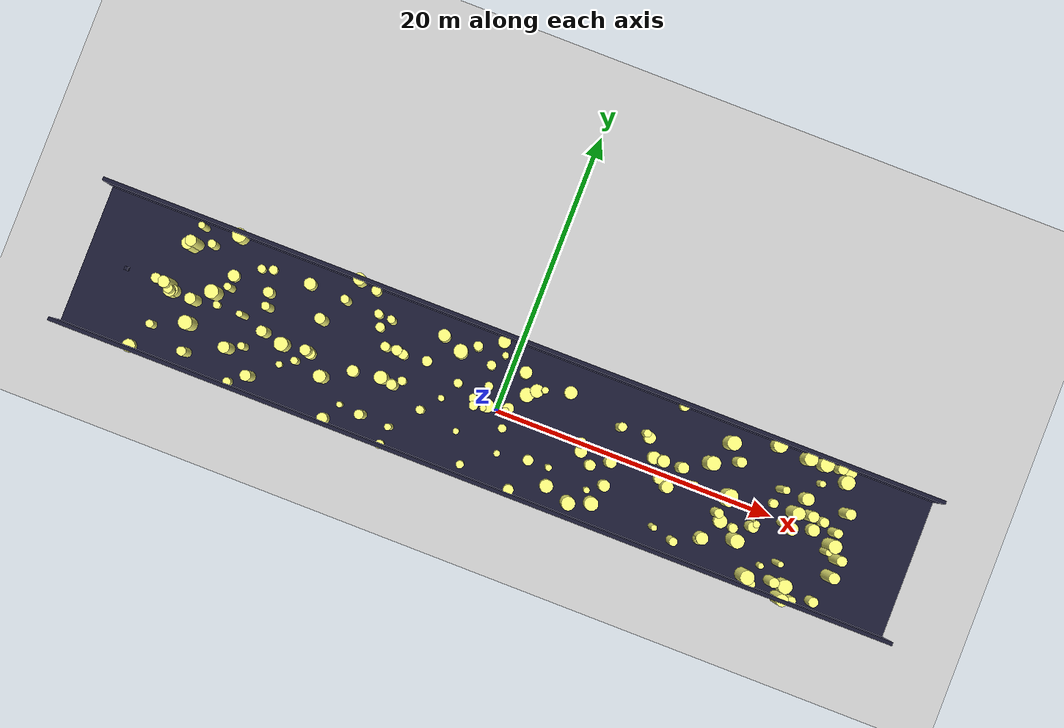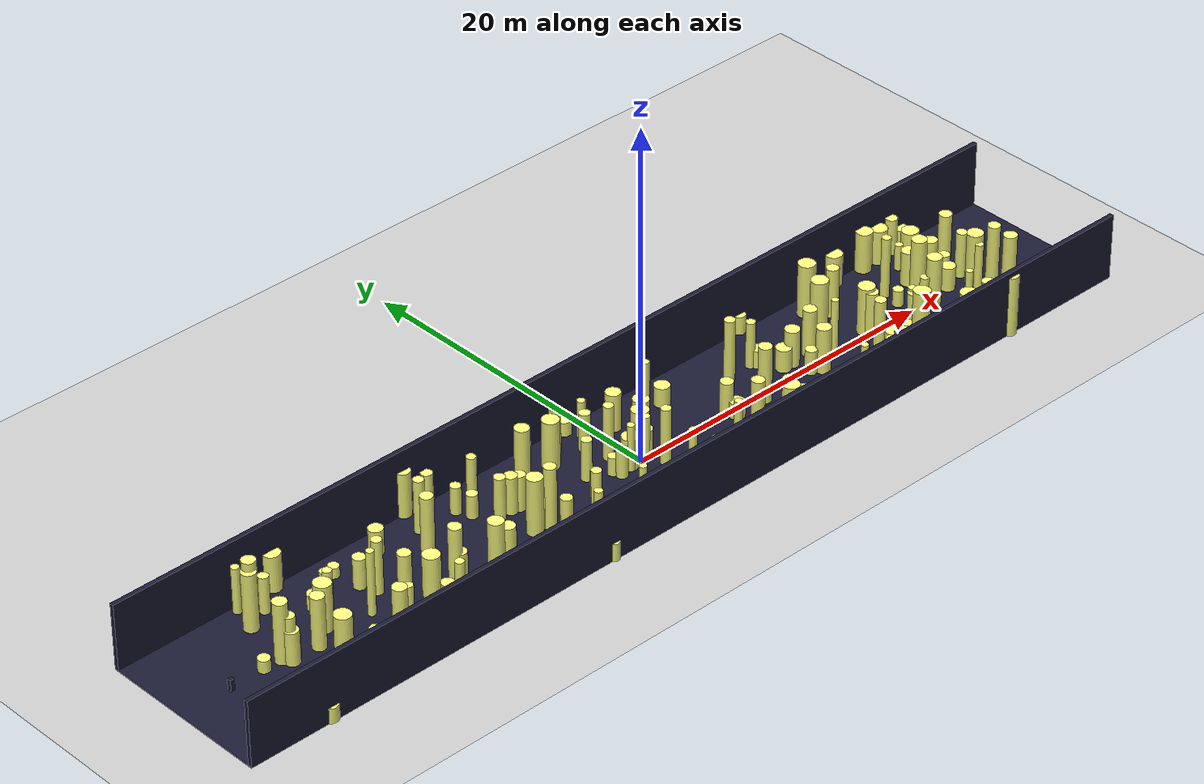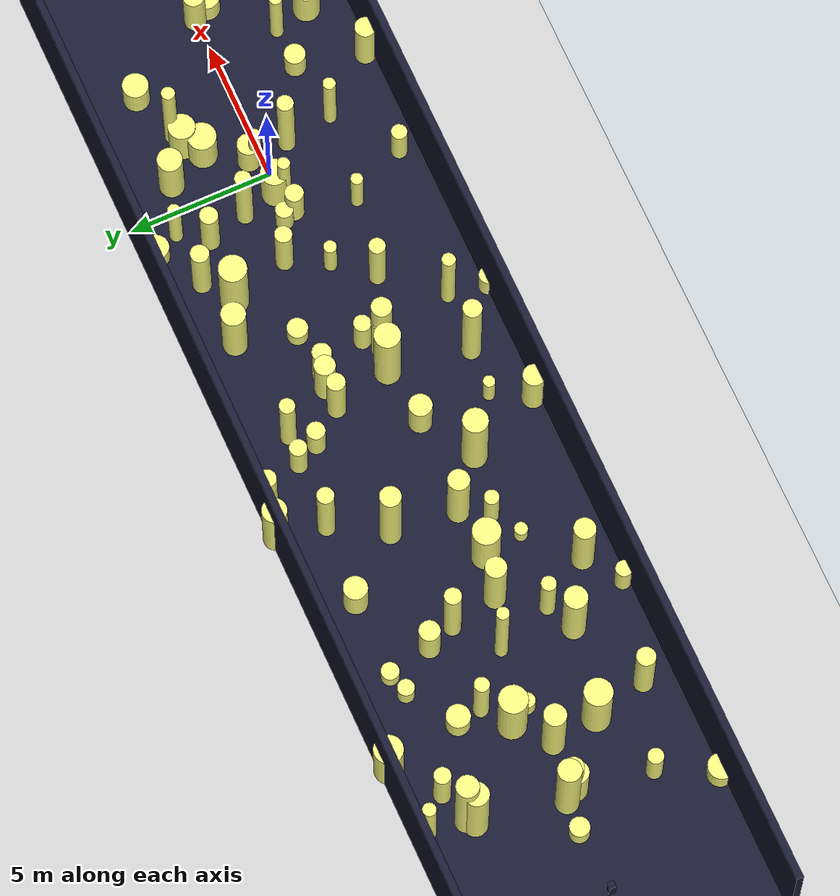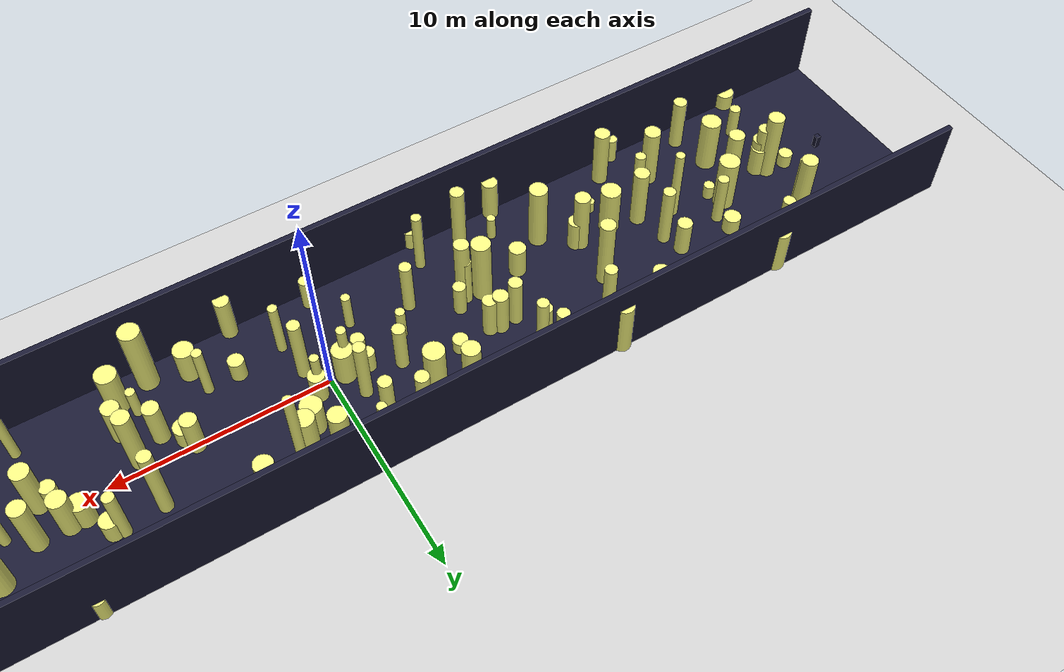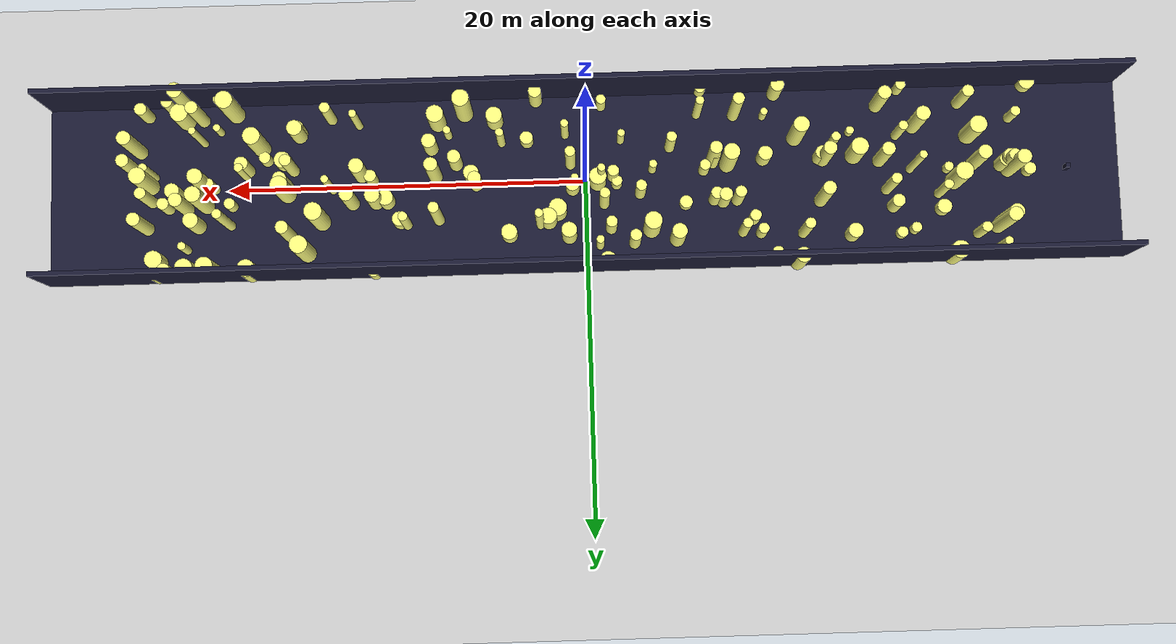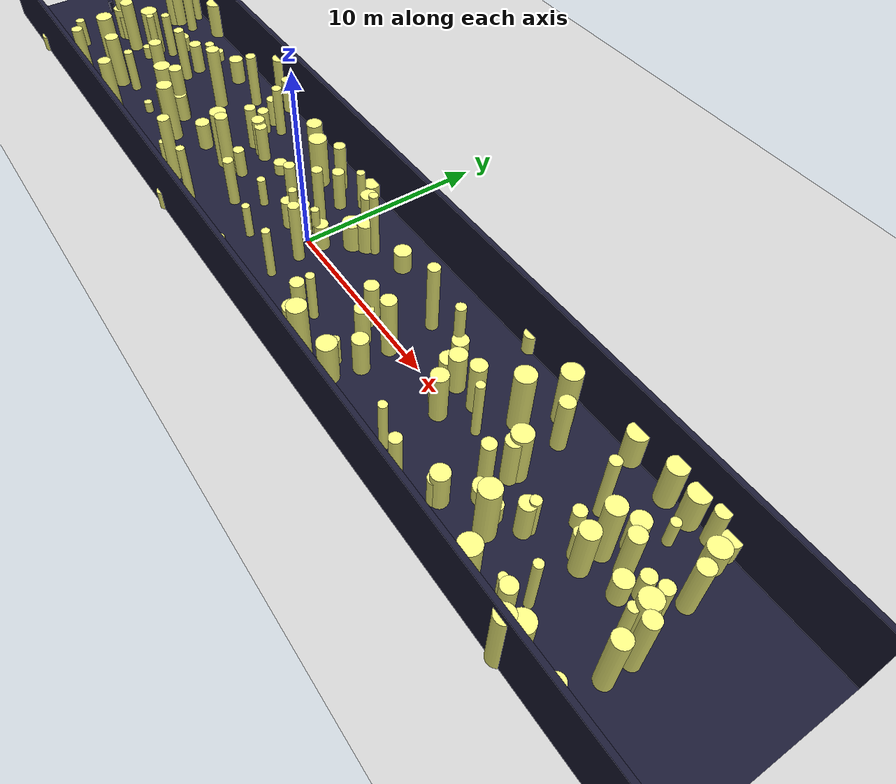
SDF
<?xml version="1.0"?>
<sdf version="1.4">
  <world name="default">
    <gui>
      <camera name="user_camera">
        <pose>-20 -30 40 0 0.66 0.83</pose>
      </camera>
    </gui>
    <include>
      <uri>model://ground_plane</uri>
    </include>
    <include>
      <uri>model://sun</uri>
    </include>
    <scene>
      <shadows>0</shadows>
    </scene>
    <model name="forest">
      <static>true</static>
      <link name="cylinder0">
        <pose>11.826677985820567 4.899971942617954 0.5869042338431527 0 0 0 </pose>
        <visual name="visual">
          <geometry>
            <cylinder>
              <radius>0.34313009285876095</radius>
              <length>1.1738084676863054</length>
            </cylinder>
          </geometry>
          <material>
            <ambient>0.6 0.6 0.6 1</ambient>
            <diffuse>1 1 0.5 1</diffuse>
            <specular>0 0 0</specular>
            <emissive>0 0 0 1</emissive>
          </material>
        </visual>
        <collision name="collision">
          <geometry>
            <cylinder>
              <radius>0.34313009285876095</radius>
              <length>1.1738084676863054</length>
            </cylinder>
          </geometry>
          <max_contacts>0</max_contacts>
        </collision>
      </link>
      <link name="cylinder1">
        <pose>11.915547671943166 -0.35116643810493464 0.7668834934920222 0 0 0 </pose>
        <visual name="visual">
          <geometry>
            <cylinder>
              <radius>0.3422690984058516</radius>
              <length>1.5337669869840445</length>
            </cylinder>
          </geometry>
          <material>
            <ambient>0.6 0.6 0.6 1</ambient>
            <diffuse>1 1 0.5 1</diffuse>
            <specular>0 0 0</specular>
            <emissive>0 0 0 1</emissive>
          </material>
        </visual>
        <collision name="collision">
          <geometry>
            <cylinder>
              <radius>0.3422690984058516</radius>
              <length>1.5337669869840445</length>
            </cylinder>
          </geometry>
          <max_contacts>0</max_contacts>
        </collision>
      </link>
      <link name="cylinder2">
        <pose>16.85352270923643 -1.5199237046814162 0.4903164582564621 0 0 0 </pose>
        <visual name="visual">
          <geometry>
            <cylinder>
              <radius>0.4697104226124172</radius>
              <length>0.9806329165129242</length>
            </cylinder>
          </geometry>
          <material>
            <ambient>0.6 0.6 0.6 1</ambient>
            <diffuse>1 1 0.5 1</diffuse>
            <specular>0 0 0</specular>
            <emissive>0 0 0 1</emissive>
          </material>
        </visual>
        <collision name="collision">
          <geometry>
            <cylinder>
              <radius>0.4697104226124172</radius>
              <length>0.9806329165129242</length>
            </cylinder>
          </geometry>
          <max_contacts>0</max_contacts>
        </collision>
      </link>
      <link name="cylinder3">
        <pose>8.377565184089626 -0.4774144621142149 1.7249580205077046 0 0 0 </pose>
        <visual name="visual">
          <geometry>
            <cylinder>
              <radius>0.3816601781571072</radius>
              <length>3.4499160410154093</length>
            </cylinder>
          </geometry>
          <material>
            <ambient>0.6 0.6 0.6 1</ambient>
            <diffuse>1 1 0.5 1</diffuse>
            <specular>0 0 0</specular>
            <emissive>0 0 0 1</emissive>
          </material>
        </visual>
        <collision name="collision">
          <geometry>
            <cylinder>
              <radius>0.3816601781571072</radius>
              <length>3.4499160410154093</length>
            </cylinder>
          </geometry>
          <max_contacts>0</max_contacts>
        </collision>
      </link>
      <link name="cylinder4">
        <pose>15.882903146454112 -3.1812900634328556 0.8596063217194532 0 0 0 </pose>
        <visual name="visual">
          <geometry>
            <cylinder>
              <radius>0.34671603202420453</radius>
              <length>1.7192126434389063</length>
            </cylinder>
          </geometry>
          <material>
            <ambient>0.6 0.6 0.6 1</ambient>
            <diffuse>1 1 0.5 1</diffuse>
            <specular>0 0 0</specular>
            <emissive>0 0 0 1</emissive>
          </material>
        </visual>
        <collision name="collision">
          <geometry>
            <cylinder>
              <radius>0.34671603202420453</radius>
              <length>1.7192126434389063</length>
            </cylinder>
          </geometry>
          <max_contacts>0</max_contacts>
        </collision>
      </link>
      <link name="cylinder5">
        <pose>-14.917778410111532 -2.365029276385857 0.33924573023969384 0 0 0 </pose>
        <visual name="visual">
          <geometry>
            <cylinder>
              <radius>0.22715811138292039</radius>
              <length>0.6784914604793877</length>
            </cylinder>
          </geometry>
          <material>
            <ambient>0.6 0.6 0.6 1</ambient>
            <diffuse>1 1 0.5 1</diffuse>
            <specular>0 0 0</specular>
            <emissive>0 0 0 1</emissive>
          </material>
        </visual>
        <collision name="collision">
          <geometry>
            <cylinder>
              <radius>0.22715811138292039</radius>
              <length>0.6784914604793877</length>
            </cylinder>
          </geometry>
          <max_contacts>0</max_contacts>
        </collision>
      </link>
      <link name="cylinder6">
        <pose>-19.81368941153287 1.2810669564978836 1.3848295582383636 0 0 0 </pose>
        <visual name="visual">
          <geometry>
            <cylinder>
              <radius>0.25956951055257527</radius>
              <length>2.7696591164767272</length>
            </cylinder>
          </geometry>
          <material>
            <ambient>0.6 0.6 0.6 1</ambient>
            <diffuse>1 1 0.5 1</diffuse>
            <specular>0 0 0</specular>
            <emissive>0 0 0 1</emissive>
          </material>
        </visual>
        <collision name="collision">
          <geometry>
            <cylinder>
              <radius>0.25956951055257527</radius>
              <length>2.7696591164767272</length>
            </cylinder>
          </geometry>
          <max_contacts>0</max_contacts>
        </collision>
      </link>
      <link name="cylinder7">
        <pose>-4.7892316451903625 -1.782252144681995 1.4149924909686387 0 0 0 </pose>
        <visual name="visual">
          <geometry>
            <cylinder>
              <radius>0.282575552453872</radius>
              <length>2.8299849819372773</length>
            </cylinder>
          </geometry>
          <material>
            <ambient>0.6 0.6 0.6 1</ambient>
            <diffuse>1 1 0.5 1</diffuse>
            <specular>0 0 0</specular>
            <emissive>0 0 0 1</emissive>
          </material>
        </visual>
        <collision name="collision">
          <geometry>
            <cylinder>
              <radius>0.282575552453872</radius>
              <length>2.8299849819372773</length>
            </cylinder>
          </geometry>
          <max_contacts>0</max_contacts>
        </collision>
      </link>
      <link name="cylinder8">
        <pose>-3.6448727700532153 2.8580336375987603 1.4945671176735664 0 0 0 </pose>
        <visual name="visual">
          <geometry>
            <cylinder>
              <radius>0.4844523856458611</radius>
              <length>2.989134235347133</length>
            </cylinder>
          </geometry>
          <material>
            <ambient>0.6 0.6 0.6 1</ambient>
            <diffuse>1 1 0.5 1</diffuse>
            <specular>0 0 0</specular>
            <emissive>0 0 0 1</emissive>
          </material>
        </visual>
        <collision name="collision">
          <geometry>
            <cylinder>
              <radius>0.4844523856458611</radius>
              <length>2.989134235347133</length>
            </cylinder>
          </geometry>
          <max_contacts>0</max_contacts>
        </collision>
      </link>
      <link name="cylinder9">
        <pose>-1.1623011544158075 4.57616283363088 0.45587341599845277 0 0 0 </pose>
        <visual name="visual">
          <geometry>
            <cylinder>
              <radius>0.4354340474725951</radius>
              <length>0.9117468319969055</length>
            </cylinder>
          </geometry>
          <material>
            <ambient>0.6 0.6 0.6 1</ambient>
            <diffuse>1 1 0.5 1</diffuse>
            <specular>0 0 0</specular>
            <emissive>0 0 0 1</emissive>
          </material>
        </visual>
        <collision name="collision">
          <geometry>
            <cylinder>
              <radius>0.4354340474725951</radius>
              <length>0.9117468319969055</length>
            </cylinder>
          </geometry>
          <max_contacts>0</max_contacts>
        </collision>
      </link>
      <link name="cylinder10">
        <pose>21.23232838670821 0.8351597643573729 1.8041299638507438 0 0 0 </pose>
        <visual name="visual">
          <geometry>
            <cylinder>
              <radius>0.43971690417877474</radius>
              <length>3.6082599277014875</length>
            </cylinder>
          </geometry>
          <material>
            <ambient>0.6 0.6 0.6 1</ambient>
            <diffuse>1 1 0.5 1</diffuse>
            <specular>0 0 0</specular>
            <emissive>0 0 0 1</emissive>
          </material>
        </visual>
        <collision name="collision">
          <geometry>
            <cylinder>
              <radius>0.43971690417877474</radius>
              <length>3.6082599277014875</length>
            </cylinder>
          </geometry>
          <max_contacts>0</max_contacts>
        </collision>
      </link>
      <link name="cylinder11">
        <pose>-3.7788375125863816 -0.5392359730300118 0.8549719906756208 0 0 0 </pose>
        <visual name="visual">
          <geometry>
            <cylinder>
              <radius>0.2205920576685439</radius>
              <length>1.7099439813512416</length>
            </cylinder>
          </geometry>
          <material>
            <ambient>0.6 0.6 0.6 1</ambient>
            <diffuse>1 1 0.5 1</diffuse>
            <specular>0 0 0</specular>
            <emissive>0 0 0 1</emissive>
          </material>
        </visual>
        <collision name="collision">
          <geometry>
            <cylinder>
              <radius>0.2205920576685439</radius>
              <length>1.7099439813512416</length>
            </cylinder>
          </geometry>
          <max_contacts>0</max_contacts>
        </collision>
      </link>
      <link name="cylinder12">
        <pose>-6.6620790563027725 -0.4087574144002133 0.8482972163667704 0 0 0 </pose>
        <visual name="visual">
          <geometry>
            <cylinder>
              <radius>0.2986509980933311</radius>
              <length>1.6965944327335407</length>
            </cylinder>
          </geometry>
          <material>
            <ambient>0.6 0.6 0.6 1</ambient>
            <diffuse>1 1 0.5 1</diffuse>
            <specular>0 0 0</specular>
            <emissive>0 0 0 1</emissive>
          </material>
        </visual>
        <collision name="collision">
          <geometry>
            <cylinder>
              <radius>0.2986509980933311</radius>
              <length>1.6965944327335407</length>
            </cylinder>
          </geometry>
          <max_contacts>0</max_contacts>
        </collision>
      </link>
      <link name="cylinder13">
        <pose>17.81148508534315 -1.6497905022994708 0.535257738188236 0 0 0 </pose>
        <visual name="visual">
          <geometry>
            <cylinder>
              <radius>0.3235462991837572</radius>
              <length>1.070515476376472</length>
            </cylinder>
          </geometry>
          <material>
            <ambient>0.6 0.6 0.6 1</ambient>
            <diffuse>1 1 0.5 1</diffuse>
            <specular>0 0 0</specular>
            <emissive>0 0 0 1</emissive>
          </material>
        </visual>
        <collision name="collision">
          <geometry>
            <cylinder>
              <radius>0.3235462991837572</radius>
              <length>1.070515476376472</length>
            </cylinder>
          </geometry>
          <max_contacts>0</max_contacts>
        </collision>
      </link>
      <link name="cylinder14">
        <pose>6.68073826129892 -4.050243944122489 1.8426344751059494 0 0 0 </pose>
        <visual name="visual">
          <geometry>
            <cylinder>
              <radius>0.4736189609778217</radius>
              <length>3.6852689502118987</length>
            </cylinder>
          </geometry>
          <material>
            <ambient>0.6 0.6 0.6 1</ambient>
            <diffuse>1 1 0.5 1</diffuse>
            <specular>0 0 0</specular>
            <emissive>0 0 0 1</emissive>
          </material>
        </visual>
        <collision name="collision">
          <geometry>
            <cylinder>
              <radius>0.4736189609778217</radius>
              <length>3.6852689502118987</length>
            </cylinder>
          </geometry>
          <max_contacts>0</max_contacts>
        </collision>
      </link>
      <link name="cylinder15">
        <pose>16.54110975923666 2.6736107362665074 1.5243468116367418 0 0 0 </pose>
        <visual name="visual">
          <geometry>
            <cylinder>
              <radius>0.3569002195849709</radius>
              <length>3.0486936232734836</length>
            </cylinder>
          </geometry>
          <material>
            <ambient>0.6 0.6 0.6 1</ambient>
            <diffuse>1 1 0.5 1</diffuse>
            <specular>0 0 0</specular>
            <emissive>0 0 0 1</emissive>
          </material>
        </visual>
        <collision name="collision">
          <geometry>
            <cylinder>
              <radius>0.3569002195849709</radius>
              <length>3.0486936232734836</length>
            </cylinder>
          </geometry>
          <max_contacts>0</max_contacts>
        </collision>
      </link>
      <link name="cylinder16">
        <pose>2.562045674358533 2.4284179138466566 1.8893746194092786 0 0 0 </pose>
        <visual name="visual">
          <geometry>
            <cylinder>
              <radius>0.23251905358783606</radius>
              <length>3.7787492388185573</length>
            </cylinder>
          </geometry>
          <material>
            <ambient>0.6 0.6 0.6 1</ambient>
            <diffuse>1 1 0.5 1</diffuse>
            <specular>0 0 0</specular>
            <emissive>0 0 0 1</emissive>
          </material>
        </visual>
        <collision name="collision">
          <geometry>
            <cylinder>
              <radius>0.23251905358783606</radius>
              <length>3.7787492388185573</length>
            </cylinder>
          </geometry>
          <max_contacts>0</max_contacts>
        </collision>
      </link>
      <link name="cylinder17">
        <pose>14.164843109316365 -3.9189205243046086 1.4657657977281235 0 0 0 </pose>
        <visual name="visual">
          <geometry>
            <cylinder>
              <radius>0.29147691392387615</radius>
              <length>2.931531595456247</length>
            </cylinder>
          </geometry>
          <material>
            <ambient>0.6 0.6 0.6 1</ambient>
            <diffuse>1 1 0.5 1</diffuse>
            <specular>0 0 0</specular>
            <emissive>0 0 0 1</emissive>
          </material>
        </visual>
        <collision name="collision">
          <geometry>
            <cylinder>
              <radius>0.29147691392387615</radius>
              <length>2.931531595456247</length>
            </cylinder>
          </geometry>
          <max_contacts>0</max_contacts>
        </collision>
      </link>
      <link name="cylinder18">
        <pose>22.081934669884475 4.589553546037964 1.0865761649251073 0 0 0 </pose>
        <visual name="visual">
          <geometry>
            <cylinder>
              <radius>0.4905206526309489</radius>
              <length>2.1731523298502147</length>
            </cylinder>
          </geometry>
          <material>
            <ambient>0.6 0.6 0.6 1</ambient>
            <diffuse>1 1 0.5 1</diffuse>
            <specular>0 0 0</specular>
            <emissive>0 0 0 1</emissive>
          </material>
        </visual>
        <collision name="collision">
          <geometry>
            <cylinder>
              <radius>0.4905206526309489</radius>
              <length>2.1731523298502147</length>
            </cylinder>
          </geometry>
          <max_contacts>0</max_contacts>
        </collision>
      </link>
      <link name="cylinder19">
        <pose>19.017382186992116 -0.8356951410971831 1.1742498988828127 0 0 0 </pose>
        <visual name="visual">
          <geometry>
            <cylinder>
              <radius>0.2438730452608467</radius>
              <length>2.3484997977656255</length>
            </cylinder>
          </geometry>
          <material>
            <ambient>0.6 0.6 0.6 1</ambient>
            <diffuse>1 1 0.5 1</diffuse>
            <specular>0 0 0</specular>
            <emissive>0 0 0 1</emissive>
          </material>
        </visual>
        <collision name="collision">
          <geometry>
            <cylinder>
              <radius>0.2438730452608467</radius>
              <length>2.3484997977656255</length>
            </cylinder>
          </geometry>
          <max_contacts>0</max_contacts>
        </collision>
      </link>
      <link name="cylinder20">
        <pose>22.88792815418561 0.1683337289828266 0.7526996093904776 0 0 0 </pose>
        <visual name="visual">
          <geometry>
            <cylinder>
              <radius>0.4192804516614004</radius>
              <length>1.5053992187809553</length>
            </cylinder>
          </geometry>
          <material>
            <ambient>0.6 0.6 0.6 1</ambient>
            <diffuse>1 1 0.5 1</diffuse>
            <specular>0 0 0</specular>
            <emissive>0 0 0 1</emissive>
          </material>
        </visual>
        <collision name="collision">
          <geometry>
            <cylinder>
              <radius>0.4192804516614004</radius>
              <length>1.5053992187809553</length>
            </cylinder>
          </geometry>
          <max_contacts>0</max_contacts>
        </collision>
      </link>
      <link name="cylinder21">
        <pose>23.351556238140013 0.9211427524844691 0.8247973887835952 0 0 0 </pose>
        <visual name="visual">
          <geometry>
            <cylinder>
              <radius>0.3324104645225271</radius>
              <length>1.6495947775671904</length>
            </cylinder>
          </geometry>
          <material>
            <ambient>0.6 0.6 0.6 1</ambient>
            <diffuse>1 1 0.5 1</diffuse>
            <specular>0 0 0</specular>
            <emissive>0 0 0 1</emissive>
          </material>
        </visual>
        <collision name="collision">
          <geometry>
            <cylinder>
              <radius>0.3324104645225271</radius>
              <length>1.6495947775671904</length>
            </cylinder>
          </geometry>
          <max_contacts>0</max_contacts>
        </collision>
      </link>
      <link name="cylinder22">
        <pose>-5.058869025532459 3.4578576876256015 1.4231111228881201 0 0 0 </pose>
        <visual name="visual">
          <geometry>
            <cylinder>
              <radius>0.4195538924439936</radius>
              <length>2.8462222457762403</length>
            </cylinder>
          </geometry>
          <material>
            <ambient>0.6 0.6 0.6 1</ambient>
            <diffuse>1 1 0.5 1</diffuse>
            <specular>0 0 0</specular>
            <emissive>0 0 0 1</emissive>
          </material>
        </visual>
        <collision name="collision">
          <geometry>
            <cylinder>
              <radius>0.4195538924439936</radius>
              <length>2.8462222457762403</length>
            </cylinder>
          </geometry>
          <max_contacts>0</max_contacts>
        </collision>
      </link>
      <link name="cylinder23">
        <pose>-14.84910226127406 3.4780006436737807 0.7836656961386094 0 0 0 </pose>
        <visual name="visual">
          <geometry>
            <cylinder>
              <radius>0.41026654295973275</radius>
              <length>1.5673313922772187</length>
            </cylinder>
          </geometry>
          <material>
            <ambient>0.6 0.6 0.6 1</ambient>
            <diffuse>1 1 0.5 1</diffuse>
            <specular>0 0 0</specular>
            <emissive>0 0 0 1</emissive>
          </material>
        </visual>
        <collision name="collision">
          <geometry>
            <cylinder>
              <radius>0.41026654295973275</radius>
              <length>1.5673313922772187</length>
            </cylinder>
          </geometry>
          <max_contacts>0</max_contacts>
        </collision>
      </link>
      <link name="cylinder24">
        <pose>22.31656505410222 0.9966041452287433 1.5043619795012289 0 0 0 </pose>
        <visual name="visual">
          <geometry>
            <cylinder>
              <radius>0.37787404373720535</radius>
              <length>3.0087239590024577</length>
            </cylinder>
          </geometry>
          <material>
            <ambient>0.6 0.6 0.6 1</ambient>
            <diffuse>1 1 0.5 1</diffuse>
            <specular>0 0 0</specular>
            <emissive>0 0 0 1</emissive>
          </material>
        </visual>
        <collision name="collision">
          <geometry>
            <cylinder>
              <radius>0.37787404373720535</radius>
              <length>3.0087239590024577</length>
            </cylinder>
          </geometry>
          <max_contacts>0</max_contacts>
        </collision>
      </link>
      <link name="cylinder25">
        <pose>19.55090622510535 -4.3614144590137185 1.7583003879640684 0 0 0 </pose>
        <visual name="visual">
          <geometry>
            <cylinder>
              <radius>0.4865441799256325</radius>
              <length>3.516600775928137</length>
            </cylinder>
          </geometry>
          <material>
            <ambient>0.6 0.6 0.6 1</ambient>
            <diffuse>1 1 0.5 1</diffuse>
            <specular>0 0 0</specular>
            <emissive>0 0 0 1</emissive>
          </material>
        </visual>
        <collision name="collision">
          <geometry>
            <cylinder>
              <radius>0.4865441799256325</radius>
              <length>3.516600775928137</length>
            </cylinder>
          </geometry>
          <max_contacts>0</max_contacts>
        </collision>
      </link>
      <link name="cylinder26">
        <pose>-8.752198740586898 3.168655074511653 1.5249935512294304 0 0 0 </pose>
        <visual name="visual">
          <geometry>
            <cylinder>
              <radius>0.27012381679006403</radius>
              <length>3.0499871024588607</length>
            </cylinder>
          </geometry>
          <material>
            <ambient>0.6 0.6 0.6 1</ambient>
            <diffuse>1 1 0.5 1</diffuse>
            <specular>0 0 0</specular>
            <emissive>0 0 0 1</emissive>
          </material>
        </visual>
        <collision name="collision">
          <geometry>
            <cylinder>
              <radius>0.27012381679006403</radius>
              <length>3.0499871024588607</length>
            </cylinder>
          </geometry>
          <max_contacts>0</max_contacts>
        </collision>
      </link>
      <link name="cylinder27">
        <pose>-1.0378330110724185 1.3430629946443906 1.683671754725586 0 0 0 </pose>
        <visual name="visual">
          <geometry>
            <cylinder>
              <radius>0.28354988021213756</radius>
              <length>3.367343509451172</length>
            </cylinder>
          </geometry>
          <material>
            <ambient>0.6 0.6 0.6 1</ambient>
            <diffuse>1 1 0.5 1</diffuse>
            <specular>0 0 0</specular>
            <emissive>0 0 0 1</emissive>
          </material>
        </visual>
        <collision name="collision">
          <geometry>
            <cylinder>
              <radius>0.28354988021213756</radius>
              <length>3.367343509451172</length>
            </cylinder>
          </geometry>
          <max_contacts>0</max_contacts>
        </collision>
      </link>
      <link name="cylinder28">
        <pose>23.146198933017466 4.679830741244247 1.1499842558241922 0 0 0 </pose>
        <visual name="visual">
          <geometry>
            <cylinder>
              <radius>0.3402844666596985</radius>
              <length>2.2999685116483843</length>
            </cylinder>
          </geometry>
          <material>
            <ambient>0.6 0.6 0.6 1</ambient>
            <diffuse>1 1 0.5 1</diffuse>
            <specular>0 0 0</specular>
            <emissive>0 0 0 1</emissive>
          </material>
        </visual>
        <collision name="collision">
          <geometry>
            <cylinder>
              <radius>0.3402844666596985</radius>
              <length>2.2999685116483843</length>
            </cylinder>
          </geometry>
          <max_contacts>0</max_contacts>
        </collision>
      </link>
      <link name="cylinder29">
        <pose>-21.121205069637394 -3.870491480591812 1.4228794701995162 0 0 0 </pose>
        <visual name="visual">
          <geometry>
            <cylinder>
              <radius>0.3268050522809638</radius>
              <length>2.8457589403990324</length>
            </cylinder>
          </geometry>
          <material>
            <ambient>0.6 0.6 0.6 1</ambient>
            <diffuse>1 1 0.5 1</diffuse>
            <specular>0 0 0</specular>
            <emissive>0 0 0 1</emissive>
          </material>
        </visual>
        <collision name="collision">
          <geometry>
            <cylinder>
              <radius>0.3268050522809638</radius>
              <length>2.8457589403990324</length>
            </cylinder>
          </geometry>
          <max_contacts>0</max_contacts>
        </collision>
      </link>
      <link name="cylinder30">
        <pose>19.890360612082304 1.9825380708927103 1.8899275905680515 0 0 0 </pose>
        <visual name="visual">
          <geometry>
            <cylinder>
              <radius>0.2615858982009419</radius>
              <length>3.779855181136103</length>
            </cylinder>
          </geometry>
          <material>
            <ambient>0.6 0.6 0.6 1</ambient>
            <diffuse>1 1 0.5 1</diffuse>
            <specular>0 0 0</specular>
            <emissive>0 0 0 1</emissive>
          </material>
        </visual>
        <collision name="collision">
          <geometry>
            <cylinder>
              <radius>0.2615858982009419</radius>
              <length>3.779855181136103</length>
            </cylinder>
          </geometry>
          <max_contacts>0</max_contacts>
        </collision>
      </link>
      <link name="cylinder31">
        <pose>24.54866488244153 2.030646643357871 1.5939948637435892 0 0 0 </pose>
        <visual name="visual">
          <geometry>
            <cylinder>
              <radius>0.3694740997385906</radius>
              <length>3.1879897274871785</length>
            </cylinder>
          </geometry>
          <material>
            <ambient>0.6 0.6 0.6 1</ambient>
            <diffuse>1 1 0.5 1</diffuse>
            <specular>0 0 0</specular>
            <emissive>0 0 0 1</emissive>
          </material>
        </visual>
        <collision name="collision">
          <geometry>
            <cylinder>
              <radius>0.3694740997385906</radius>
              <length>3.1879897274871785</length>
            </cylinder>
          </geometry>
          <max_contacts>0</max_contacts>
        </collision>
      </link>
      <link name="cylinder32">
        <pose>14.145014531035635 0.15088157779923872 1.6697930069987197 0 0 0 </pose>
        <visual name="visual">
          <geometry>
            <cylinder>
              <radius>0.21219663849185866</radius>
              <length>3.3395860139974394</length>
            </cylinder>
          </geometry>
          <material>
            <ambient>0.6 0.6 0.6 1</ambient>
            <diffuse>1 1 0.5 1</diffuse>
            <specular>0 0 0</specular>
            <emissive>0 0 0 1</emissive>
          </material>
        </visual>
        <collision name="collision">
          <geometry>
            <cylinder>
              <radius>0.21219663849185866</radius>
              <length>3.3395860139974394</length>
            </cylinder>
          </geometry>
          <max_contacts>0</max_contacts>
        </collision>
      </link>
      <link name="cylinder33">
        <pose>0.7096007454045754 0.43247661946426597 0.7666937386791144 0 0 0 </pose>
        <visual name="visual">
          <geometry>
            <cylinder>
              <radius>0.38562317667492785</radius>
              <length>1.5333874773582288</length>
            </cylinder>
          </geometry>
          <material>
            <ambient>0.6 0.6 0.6 1</ambient>
            <diffuse>1 1 0.5 1</diffuse>
            <specular>0 0 0</specular>
            <emissive>0 0 0 1</emissive>
          </material>
        </visual>
        <collision name="collision">
          <geometry>
            <cylinder>
              <radius>0.38562317667492785</radius>
              <length>1.5333874773582288</length>
            </cylinder>
          </geometry>
          <max_contacts>0</max_contacts>
        </collision>
      </link>
      <link name="cylinder34">
        <pose>-20.69903656651999 0.5843863166121688 1.4367598693355228 0 0 0 </pose>
        <visual name="visual">
          <geometry>
            <cylinder>
              <radius>0.4882078344602088</radius>
              <length>2.8735197386710456</length>
            </cylinder>
          </geometry>
          <material>
            <ambient>0.6 0.6 0.6 1</ambient>
            <diffuse>1 1 0.5 1</diffuse>
            <specular>0 0 0</specular>
            <emissive>0 0 0 1</emissive>
          </material>
        </visual>
        <collision name="collision">
          <geometry>
            <cylinder>
              <radius>0.4882078344602088</radius>
              <length>2.8735197386710456</length>
            </cylinder>
          </geometry>
          <max_contacts>0</max_contacts>
        </collision>
      </link>
      <link name="cylinder35">
        <pose>18.1018515098012 -2.358989871626643 1.6671822992722356 0 0 0 </pose>
        <visual name="visual">
          <geometry>
            <cylinder>
              <radius>0.4823512788014799</radius>
              <length>3.334364598544471</length>
            </cylinder>
          </geometry>
          <material>
            <ambient>0.6 0.6 0.6 1</ambient>
            <diffuse>1 1 0.5 1</diffuse>
            <specular>0 0 0</specular>
            <emissive>0 0 0 1</emissive>
          </material>
        </visual>
        <collision name="collision">
          <geometry>
            <cylinder>
              <radius>0.4823512788014799</radius>
              <length>3.334364598544471</length>
            </cylinder>
          </geometry>
          <max_contacts>0</max_contacts>
        </collision>
      </link>
      <link name="cylinder36">
        <pose>-1.394635543051077 2.7415323315756783 1.183814106745353 0 0 0 </pose>
        <visual name="visual">
          <geometry>
            <cylinder>
              <radius>0.3163471055712237</radius>
              <length>2.367628213490706</length>
            </cylinder>
          </geometry>
          <material>
            <ambient>0.6 0.6 0.6 1</ambient>
            <diffuse>1 1 0.5 1</diffuse>
            <specular>0 0 0</specular>
            <emissive>0 0 0 1</emissive>
          </material>
        </visual>
        <collision name="collision">
          <geometry>
            <cylinder>
              <radius>0.3163471055712237</radius>
              <length>2.367628213490706</length>
            </cylinder>
          </geometry>
          <max_contacts>0</max_contacts>
        </collision>
      </link>
      <link name="cylinder37">
        <pose>23.126579535795926 -4.808531130241135 0.8421003473515796 0 0 0 </pose>
        <visual name="visual">
          <geometry>
            <cylinder>
              <radius>0.31169881950522427</radius>
              <length>1.6842006947031591</length>
            </cylinder>
          </geometry>
          <material>
            <ambient>0.6 0.6 0.6 1</ambient>
            <diffuse>1 1 0.5 1</diffuse>
            <specular>0 0 0</specular>
            <emissive>0 0 0 1</emissive>
          </material>
        </visual>
        <collision name="collision">
          <geometry>
            <cylinder>
              <radius>0.31169881950522427</radius>
              <length>1.6842006947031591</length>
            </cylinder>
          </geometry>
          <max_contacts>0</max_contacts>
        </collision>
      </link>
      <link name="cylinder38">
        <pose>22.210281383809615 -4.933315609613817 1.826320196705377 0 0 0 </pose>
        <visual name="visual">
          <geometry>
            <cylinder>
              <radius>0.423259821530241</radius>
              <length>3.652640393410754</length>
            </cylinder>
          </geometry>
          <material>
            <ambient>0.6 0.6 0.6 1</ambient>
            <diffuse>1 1 0.5 1</diffuse>
            <specular>0 0 0</specular>
            <emissive>0 0 0 1</emissive>
          </material>
        </visual>
        <collision name="collision">
          <geometry>
            <cylinder>
              <radius>0.423259821530241</radius>
              <length>3.652640393410754</length>
            </cylinder>
          </geometry>
          <max_contacts>0</max_contacts>
        </collision>
      </link>
      <link name="cylinder39">
        <pose>-23.253010785968282 3.0240801046155195 1.7640948192729184 0 0 0 </pose>
        <visual name="visual">
          <geometry>
            <cylinder>
              <radius>0.41207023708942214</radius>
              <length>3.528189638545837</length>
            </cylinder>
          </geometry>
          <material>
            <ambient>0.6 0.6 0.6 1</ambient>
            <diffuse>1 1 0.5 1</diffuse>
            <specular>0 0 0</specular>
            <emissive>0 0 0 1</emissive>
          </material>
        </visual>
        <collision name="collision">
          <geometry>
            <cylinder>
              <radius>0.41207023708942214</radius>
              <length>3.528189638545837</length>
            </cylinder>
          </geometry>
          <max_contacts>0</max_contacts>
        </collision>
      </link>
      <link name="cylinder40">
        <pose>20.753949416310192 -0.10957031323516109 0.9394621256935985 0 0 0 </pose>
        <visual name="visual">
          <geometry>
            <cylinder>
              <radius>0.26863239323546817</radius>
              <length>1.878924251387197</length>
            </cylinder>
          </geometry>
          <material>
            <ambient>0.6 0.6 0.6 1</ambient>
            <diffuse>1 1 0.5 1</diffuse>
            <specular>0 0 0</specular>
            <emissive>0 0 0 1</emissive>
          </material>
        </visual>
        <collision name="collision">
          <geometry>
            <cylinder>
              <radius>0.26863239323546817</radius>
              <length>1.878924251387197</length>
            </cylinder>
          </geometry>
          <max_contacts>0</max_contacts>
        </collision>
      </link>
      <link name="cylinder41">
        <pose>13.053319407883997 0.9175047944221646 1.4601352081956382 0 0 0 </pose>
        <visual name="visual">
          <geometry>
            <cylinder>
              <radius>0.3889727540429673</radius>
              <length>2.9202704163912765</length>
            </cylinder>
          </geometry>
          <material>
            <ambient>0.6 0.6 0.6 1</ambient>
            <diffuse>1 1 0.5 1</diffuse>
            <specular>0 0 0</specular>
            <emissive>0 0 0 1</emissive>
          </material>
        </visual>
        <collision name="collision">
          <geometry>
            <cylinder>
              <radius>0.3889727540429673</radius>
              <length>2.9202704163912765</length>
            </cylinder>
          </geometry>
          <max_contacts>0</max_contacts>
        </collision>
      </link>
      <link name="cylinder42">
        <pose>21.37751205461204 -4.05521436788613 1.6159200462265029 0 0 0 </pose>
        <visual name="visual">
          <geometry>
            <cylinder>
              <radius>0.3512687478570553</radius>
              <length>3.2318400924530057</length>
            </cylinder>
          </geometry>
          <material>
            <ambient>0.6 0.6 0.6 1</ambient>
            <diffuse>1 1 0.5 1</diffuse>
            <specular>0 0 0</specular>
            <emissive>0 0 0 1</emissive>
          </material>
        </visual>
        <collision name="collision">
          <geometry>
            <cylinder>
              <radius>0.3512687478570553</radius>
              <length>3.2318400924530057</length>
            </cylinder>
          </geometry>
          <max_contacts>0</max_contacts>
        </collision>
      </link>
      <link name="cylinder43">
        <pose>-21.91760564130516 3.5991199583601965 1.1309483220547603 0 0 0 </pose>
        <visual name="visual">
          <geometry>
            <cylinder>
              <radius>0.2883203636898688</radius>
              <length>2.2618966441095205</length>
            </cylinder>
          </geometry>
          <material>
            <ambient>0.6 0.6 0.6 1</ambient>
            <diffuse>1 1 0.5 1</diffuse>
            <specular>0 0 0</specular>
            <emissive>0 0 0 1</emissive>
          </material>
        </visual>
        <collision name="collision">
          <geometry>
            <cylinder>
              <radius>0.2883203636898688</radius>
              <length>2.2618966441095205</length>
            </cylinder>
          </geometry>
          <max_contacts>0</max_contacts>
        </collision>
      </link>
      <link name="cylinder44">
        <pose>6.353562092089117 -0.5031696292536649 0.5001863215971156 0 0 0 </pose>
        <visual name="visual">
          <geometry>
            <cylinder>
              <radius>0.43484996114699337</radius>
              <length>1.0003726431942312</length>
            </cylinder>
          </geometry>
          <material>
            <ambient>0.6 0.6 0.6 1</ambient>
            <diffuse>1 1 0.5 1</diffuse>
            <specular>0 0 0</specular>
            <emissive>0 0 0 1</emissive>
          </material>
        </visual>
        <collision name="collision">
          <geometry>
            <cylinder>
              <radius>0.43484996114699337</radius>
              <length>1.0003726431942312</length>
            </cylinder>
          </geometry>
          <max_contacts>0</max_contacts>
        </collision>
      </link>
      <link name="cylinder45">
        <pose>16.693918618681884 -0.07840284378698215 1.3955045873859342 0 0 0 </pose>
        <visual name="visual">
          <geometry>
            <cylinder>
              <radius>0.37877313525698275</radius>
              <length>2.7910091747718684</length>
            </cylinder>
          </geometry>
          <material>
            <ambient>0.6 0.6 0.6 1</ambient>
            <diffuse>1 1 0.5 1</diffuse>
            <specular>0 0 0</specular>
            <emissive>0 0 0 1</emissive>
          </material>
        </visual>
        <collision name="collision">
          <geometry>
            <cylinder>
              <radius>0.37877313525698275</radius>
              <length>2.7910091747718684</length>
            </cylinder>
          </geometry>
          <max_contacts>0</max_contacts>
        </collision>
      </link>
      <link name="cylinder46">
        <pose>-13.92909294932756 -1.7483290615901192 0.9566677059769797 0 0 0 </pose>
        <visual name="visual">
          <geometry>
            <cylinder>
              <radius>0.25561517409674783</radius>
              <length>1.9133354119539594</length>
            </cylinder>
          </geometry>
          <material>
            <ambient>0.6 0.6 0.6 1</ambient>
            <diffuse>1 1 0.5 1</diffuse>
            <specular>0 0 0</specular>
            <emissive>0 0 0 1</emissive>
          </material>
        </visual>
        <collision name="collision">
          <geometry>
            <cylinder>
              <radius>0.25561517409674783</radius>
              <length>1.9133354119539594</length>
            </cylinder>
          </geometry>
          <max_contacts>0</max_contacts>
        </collision>
      </link>
      <link name="cylinder47">
        <pose>24.475181988496644 -4.354331795640624 1.020487259942327 0 0 0 </pose>
        <visual name="visual">
          <geometry>
            <cylinder>
              <radius>0.3433122116981998</radius>
              <length>2.040974519884654</length>
            </cylinder>
          </geometry>
          <material>
            <ambient>0.6 0.6 0.6 1</ambient>
            <diffuse>1 1 0.5 1</diffuse>
            <specular>0 0 0</specular>
            <emissive>0 0 0 1</emissive>
          </material>
        </visual>
        <collision name="collision">
          <geometry>
            <cylinder>
              <radius>0.3433122116981998</radius>
              <length>2.040974519884654</length>
            </cylinder>
          </geometry>
          <max_contacts>0</max_contacts>
        </collision>
      </link>
      <link name="cylinder48">
        <pose>-15.11336400138616 -1.018589655266048 1.27356760379491 0 0 0 </pose>
        <visual name="visual">
          <geometry>
            <cylinder>
              <radius>0.4801093974047901</radius>
              <length>2.54713520758982</length>
            </cylinder>
          </geometry>
          <material>
            <ambient>0.6 0.6 0.6 1</ambient>
            <diffuse>1 1 0.5 1</diffuse>
            <specular>0 0 0</specular>
            <emissive>0 0 0 1</emissive>
          </material>
        </visual>
        <collision name="collision">
          <geometry>
            <cylinder>
              <radius>0.4801093974047901</radius>
              <length>2.54713520758982</length>
            </cylinder>
          </geometry>
          <max_contacts>0</max_contacts>
        </collision>
      </link>
      <link name="cylinder49">
        <pose>24.99297741693657 -1.1004772562330256 1.8646785672179182 0 0 0 </pose>
        <visual name="visual">
          <geometry>
            <cylinder>
              <radius>0.35521813960646176</radius>
              <length>3.7293571344358365</length>
            </cylinder>
          </geometry>
          <material>
            <ambient>0.6 0.6 0.6 1</ambient>
            <diffuse>1 1 0.5 1</diffuse>
            <specular>0 0 0</specular>
            <emissive>0 0 0 1</emissive>
          </material>
        </visual>
        <collision name="collision">
          <geometry>
            <cylinder>
              <radius>0.35521813960646176</radius>
              <length>3.7293571344358365</length>
            </cylinder>
          </geometry>
          <max_contacts>0</max_contacts>
        </collision>
      </link>
      <link name="cylinder50">
        <pose>-20.33666699858231 -0.12110289623878856 0.40157781722106595 0 0 0 </pose>
        <visual name="visual">
          <geometry>
            <cylinder>
              <radius>0.26024860743227995</radius>
              <length>0.8031556344421319</length>
            </cylinder>
          </geometry>
          <material>
            <ambient>0.6 0.6 0.6 1</ambient>
            <diffuse>1 1 0.5 1</diffuse>
            <specular>0 0 0</specular>
            <emissive>0 0 0 1</emissive>
          </material>
        </visual>
        <collision name="collision">
          <geometry>
            <cylinder>
              <radius>0.26024860743227995</radius>
              <length>0.8031556344421319</length>
            </cylinder>
          </geometry>
          <max_contacts>0</max_contacts>
        </collision>
      </link>
      <link name="cylinder51">
        <pose>8.585156365303128 -2.097513411166113 1.0711215126746456 0 0 0 </pose>
        <visual name="visual">
          <geometry>
            <cylinder>
              <radius>0.3970543323997602</radius>
              <length>2.1422430253492912</length>
            </cylinder>
          </geometry>
          <material>
            <ambient>0.6 0.6 0.6 1</ambient>
            <diffuse>1 1 0.5 1</diffuse>
            <specular>0 0 0</specular>
            <emissive>0 0 0 1</emissive>
          </material>
        </visual>
        <collision name="collision">
          <geometry>
            <cylinder>
              <radius>0.3970543323997602</radius>
              <length>2.1422430253492912</length>
            </cylinder>
          </geometry>
          <max_contacts>0</max_contacts>
        </collision>
      </link>
      <link name="cylinder52">
        <pose>-24.85859314895774 0.11412720701805323 0.39530089873004265 0 0 0 </pose>
        <visual name="visual">
          <geometry>
            <cylinder>
              <radius>0.34271118383837484</radius>
              <length>0.7906017974600853</length>
            </cylinder>
          </geometry>
          <material>
            <ambient>0.6 0.6 0.6 1</ambient>
            <diffuse>1 1 0.5 1</diffuse>
            <specular>0 0 0</specular>
            <emissive>0 0 0 1</emissive>
          </material>
        </visual>
        <collision name="collision">
          <geometry>
            <cylinder>
              <radius>0.34271118383837484</radius>
              <length>0.7906017974600853</length>
            </cylinder>
          </geometry>
          <max_contacts>0</max_contacts>
        </collision>
      </link>
      <link name="cylinder53">
        <pose>-24.899628249531215 -4.839318611533967 0.4535438581096857 0 0 0 </pose>
        <visual name="visual">
          <geometry>
            <cylinder>
              <radius>0.4490620625943224</radius>
              <length>0.9070877162193715</length>
            </cylinder>
          </geometry>
          <material>
            <ambient>0.6 0.6 0.6 1</ambient>
            <diffuse>1 1 0.5 1</diffuse>
            <specular>0 0 0</specular>
            <emissive>0 0 0 1</emissive>
          </material>
        </visual>
        <collision name="collision">
          <geometry>
            <cylinder>
              <radius>0.4490620625943224</radius>
              <length>0.9070877162193715</length>
            </cylinder>
          </geometry>
          <max_contacts>0</max_contacts>
        </collision>
      </link>
      <link name="cylinder54">
        <pose>19.792208910895667 0.8966879309655678 0.526436509992778 0 0 0 </pose>
        <visual name="visual">
          <geometry>
            <cylinder>
              <radius>0.3081490781120602</radius>
              <length>1.052873019985556</length>
            </cylinder>
          </geometry>
          <material>
            <ambient>0.6 0.6 0.6 1</ambient>
            <diffuse>1 1 0.5 1</diffuse>
            <specular>0 0 0</specular>
            <emissive>0 0 0 1</emissive>
          </material>
        </visual>
        <collision name="collision">
          <geometry>
            <cylinder>
              <radius>0.3081490781120602</radius>
              <length>1.052873019985556</length>
            </cylinder>
          </geometry>
          <max_contacts>0</max_contacts>
        </collision>
      </link>
      <link name="cylinder55">
        <pose>-11.753609016300286 4.9426681299936845 1.3798021303241335 0 0 0 </pose>
        <visual name="visual">
          <geometry>
            <cylinder>
              <radius>0.42295153250273115</radius>
              <length>2.759604260648267</length>
            </cylinder>
          </geometry>
          <material>
            <ambient>0.6 0.6 0.6 1</ambient>
            <diffuse>1 1 0.5 1</diffuse>
            <specular>0 0 0</specular>
            <emissive>0 0 0 1</emissive>
          </material>
        </visual>
        <collision name="collision">
          <geometry>
            <cylinder>
              <radius>0.42295153250273115</radius>
              <length>2.759604260648267</length>
            </cylinder>
          </geometry>
          <max_contacts>0</max_contacts>
        </collision>
      </link>
      <link name="cylinder56">
        <pose>7.614248750781236 -2.8064159674329137 0.8006742088423257 0 0 0 </pose>
        <visual name="visual">
          <geometry>
            <cylinder>
              <radius>0.21531449590459137</radius>
              <length>1.6013484176846513</length>
            </cylinder>
          </geometry>
          <material>
            <ambient>0.6 0.6 0.6 1</ambient>
            <diffuse>1 1 0.5 1</diffuse>
            <specular>0 0 0</specular>
            <emissive>0 0 0 1</emissive>
          </material>
        </visual>
        <collision name="collision">
          <geometry>
            <cylinder>
              <radius>0.21531449590459137</radius>
              <length>1.6013484176846513</length>
            </cylinder>
          </geometry>
          <max_contacts>0</max_contacts>
        </collision>
      </link>
      <link name="cylinder57">
        <pose>-23.50087262920758 -0.25006698706027564 1.420289328322529 0 0 0 </pose>
        <visual name="visual">
          <geometry>
            <cylinder>
              <radius>0.32541499749716796</radius>
              <length>2.840578656645058</length>
            </cylinder>
          </geometry>
          <material>
            <ambient>0.6 0.6 0.6 1</ambient>
            <diffuse>1 1 0.5 1</diffuse>
            <specular>0 0 0</specular>
            <emissive>0 0 0 1</emissive>
          </material>
        </visual>
        <collision name="collision">
          <geometry>
            <cylinder>
              <radius>0.32541499749716796</radius>
              <length>2.840578656645058</length>
            </cylinder>
          </geometry>
          <max_contacts>0</max_contacts>
        </collision>
      </link>
      <link name="cylinder58">
        <pose>8.220326605943043 1.99296571541319 1.9742979290480702 0 0 0 </pose>
        <visual name="visual">
          <geometry>
            <cylinder>
              <radius>0.3036361724176349</radius>
              <length>3.9485958580961404</length>
            </cylinder>
          </geometry>
          <material>
            <ambient>0.6 0.6 0.6 1</ambient>
            <diffuse>1 1 0.5 1</diffuse>
            <specular>0 0 0</specular>
            <emissive>0 0 0 1</emissive>
          </material>
        </visual>
        <collision name="collision">
          <geometry>
            <cylinder>
              <radius>0.3036361724176349</radius>
              <length>3.9485958580961404</length>
            </cylinder>
          </geometry>
          <max_contacts>0</max_contacts>
        </collision>
      </link>
      <link name="cylinder59">
        <pose>-16.897757245402218 0.9737711229367196 1.6436370355466692 0 0 0 </pose>
        <visual name="visual">
          <geometry>
            <cylinder>
              <radius>0.29150850356216224</radius>
              <length>3.2872740710933384</length>
            </cylinder>
          </geometry>
          <material>
            <ambient>0.6 0.6 0.6 1</ambient>
            <diffuse>1 1 0.5 1</diffuse>
            <specular>0 0 0</specular>
            <emissive>0 0 0 1</emissive>
          </material>
        </visual>
        <collision name="collision">
          <geometry>
            <cylinder>
              <radius>0.29150850356216224</radius>
              <length>3.2872740710933384</length>
            </cylinder>
          </geometry>
          <max_contacts>0</max_contacts>
        </collision>
      </link>
      <link name="cylinder60">
        <pose>4.2874149232962 2.9602339339457213 0.6199702220205348 0 0 0 </pose>
        <visual name="visual">
          <geometry>
            <cylinder>
              <radius>0.44588978340398355</radius>
              <length>1.2399404440410695</length>
            </cylinder>
          </geometry>
          <material>
            <ambient>0.6 0.6 0.6 1</ambient>
            <diffuse>1 1 0.5 1</diffuse>
            <specular>0 0 0</specular>
            <emissive>0 0 0 1</emissive>
          </material>
        </visual>
        <collision name="collision">
          <geometry>
            <cylinder>
              <radius>0.44588978340398355</radius>
              <length>1.2399404440410695</length>
            </cylinder>
          </geometry>
          <max_contacts>0</max_contacts>
        </collision>
      </link>
      <link name="cylinder61">
        <pose>-6.3656714970462005 -3.623330923076481 1.6765309125391858 0 0 0 </pose>
        <visual name="visual">
          <geometry>
            <cylinder>
              <radius>0.23369820809691802</radius>
              <length>3.3530618250783717</length>
            </cylinder>
          </geometry>
          <material>
            <ambient>0.6 0.6 0.6 1</ambient>
            <diffuse>1 1 0.5 1</diffuse>
            <specular>0 0 0</specular>
            <emissive>0 0 0 1</emissive>
          </material>
        </visual>
        <collision name="collision">
          <geometry>
            <cylinder>
              <radius>0.23369820809691802</radius>
              <length>3.3530618250783717</length>
            </cylinder>
          </geometry>
          <max_contacts>0</max_contacts>
        </collision>
      </link>
      <link name="cylinder62">
        <pose>-10.069967654731421 -3.4166140132991307 0.6626018564819176 0 0 0 </pose>
        <visual name="visual">
          <geometry>
            <cylinder>
              <radius>0.2044132507691759</radius>
              <length>1.3252037129638352</length>
            </cylinder>
          </geometry>
          <material>
            <ambient>0.6 0.6 0.6 1</ambient>
            <diffuse>1 1 0.5 1</diffuse>
            <specular>0 0 0</specular>
            <emissive>0 0 0 1</emissive>
          </material>
        </visual>
        <collision name="collision">
          <geometry>
            <cylinder>
              <radius>0.2044132507691759</radius>
              <length>1.3252037129638352</length>
            </cylinder>
          </geometry>
          <max_contacts>0</max_contacts>
        </collision>
      </link>
      <link name="cylinder63">
        <pose>15.980131105394442 -3.0378865372422847 1.065293908268392 0 0 0 </pose>
        <visual name="visual">
          <geometry>
            <cylinder>
              <radius>0.4286404402341757</radius>
              <length>2.130587816536784</length>
            </cylinder>
          </geometry>
          <material>
            <ambient>0.6 0.6 0.6 1</ambient>
            <diffuse>1 1 0.5 1</diffuse>
            <specular>0 0 0</specular>
            <emissive>0 0 0 1</emissive>
          </material>
        </visual>
        <collision name="collision">
          <geometry>
            <cylinder>
              <radius>0.4286404402341757</radius>
              <length>2.130587816536784</length>
            </cylinder>
          </geometry>
          <max_contacts>0</max_contacts>
        </collision>
      </link>
      <link name="cylinder64">
        <pose>14.781978013541071 1.9198808485765841 1.723969995079173 0 0 0 </pose>
        <visual name="visual">
          <geometry>
            <cylinder>
              <radius>0.4916619554612384</radius>
              <length>3.447939990158346</length>
            </cylinder>
          </geometry>
          <material>
            <ambient>0.6 0.6 0.6 1</ambient>
            <diffuse>1 1 0.5 1</diffuse>
            <specular>0 0 0</specular>
            <emissive>0 0 0 1</emissive>
          </material>
        </visual>
        <collision name="collision">
          <geometry>
            <cylinder>
              <radius>0.4916619554612384</radius>
              <length>3.447939990158346</length>
            </cylinder>
          </geometry>
          <max_contacts>0</max_contacts>
        </collision>
      </link>
      <link name="cylinder65">
        <pose>21.26319648621795 -0.28741031946721307 1.5076799240455494 0 0 0 </pose>
        <visual name="visual">
          <geometry>
            <cylinder>
              <radius>0.42762659130810665</radius>
              <length>3.015359848091099</length>
            </cylinder>
          </geometry>
          <material>
            <ambient>0.6 0.6 0.6 1</ambient>
            <diffuse>1 1 0.5 1</diffuse>
            <specular>0 0 0</specular>
            <emissive>0 0 0 1</emissive>
          </material>
        </visual>
        <collision name="collision">
          <geometry>
            <cylinder>
              <radius>0.42762659130810665</radius>
              <length>3.015359848091099</length>
            </cylinder>
          </geometry>
          <max_contacts>0</max_contacts>
        </collision>
      </link>
      <link name="cylinder66">
        <pose>21.333717633489854 -2.7513296253308006 1.646005594364954 0 0 0 </pose>
        <visual name="visual">
          <geometry>
            <cylinder>
              <radius>0.204460340742221</radius>
              <length>3.292011188729908</length>
            </cylinder>
          </geometry>
          <material>
            <ambient>0.6 0.6 0.6 1</ambient>
            <diffuse>1 1 0.5 1</diffuse>
            <specular>0 0 0</specular>
            <emissive>0 0 0 1</emissive>
          </material>
        </visual>
        <collision name="collision">
          <geometry>
            <cylinder>
              <radius>0.204460340742221</radius>
              <length>3.292011188729908</length>
            </cylinder>
          </geometry>
          <max_contacts>0</max_contacts>
        </collision>
      </link>
      <link name="cylinder67">
        <pose>-3.06196415271927 0.8069878091396188 1.2638531243050655 0 0 0 </pose>
        <visual name="visual">
          <geometry>
            <cylinder>
              <radius>0.2997382491270266</radius>
              <length>2.527706248610131</length>
            </cylinder>
          </geometry>
          <material>
            <ambient>0.6 0.6 0.6 1</ambient>
            <diffuse>1 1 0.5 1</diffuse>
            <specular>0 0 0</specular>
            <emissive>0 0 0 1</emissive>
          </material>
        </visual>
        <collision name="collision">
          <geometry>
            <cylinder>
              <radius>0.2997382491270266</radius>
              <length>2.527706248610131</length>
            </cylinder>
          </geometry>
          <max_contacts>0</max_contacts>
        </collision>
      </link>
      <link name="cylinder68">
        <pose>24.13885682083537 -0.8724692694396374 1.4008079089924594 0 0 0 </pose>
        <visual name="visual">
          <geometry>
            <cylinder>
              <radius>0.23481344573163077</radius>
              <length>2.801615817984919</length>
            </cylinder>
          </geometry>
          <material>
            <ambient>0.6 0.6 0.6 1</ambient>
            <diffuse>1 1 0.5 1</diffuse>
            <specular>0 0 0</specular>
            <emissive>0 0 0 1</emissive>
          </material>
        </visual>
        <collision name="collision">
          <geometry>
            <cylinder>
              <radius>0.23481344573163077</radius>
              <length>2.801615817984919</length>
            </cylinder>
          </geometry>
          <max_contacts>0</max_contacts>
        </collision>
      </link>
      <link name="cylinder69">
        <pose>0.5828403769818529 0.2471193746265179 1.2380393404211565 0 0 0 </pose>
        <visual name="visual">
          <geometry>
            <cylinder>
              <radius>0.20819283984389994</radius>
              <length>2.476078680842313</length>
            </cylinder>
          </geometry>
          <material>
            <ambient>0.6 0.6 0.6 1</ambient>
            <diffuse>1 1 0.5 1</diffuse>
            <specular>0 0 0</specular>
            <emissive>0 0 0 1</emissive>
          </material>
        </visual>
        <collision name="collision">
          <geometry>
            <cylinder>
              <radius>0.20819283984389994</radius>
              <length>2.476078680842313</length>
            </cylinder>
          </geometry>
          <max_contacts>0</max_contacts>
        </collision>
      </link>
      <link name="cylinder70">
        <pose>-2.046864401566893 -2.270482537999005 0.9949356317063305 0 0 0 </pose>
        <visual name="visual">
          <geometry>
            <cylinder>
              <radius>0.20912341714360752</radius>
              <length>1.989871263412661</length>
            </cylinder>
          </geometry>
          <material>
            <ambient>0.6 0.6 0.6 1</ambient>
            <diffuse>1 1 0.5 1</diffuse>
            <specular>0 0 0</specular>
            <emissive>0 0 0 1</emissive>
          </material>
        </visual>
        <collision name="collision">
          <geometry>
            <cylinder>
              <radius>0.20912341714360752</radius>
              <length>1.989871263412661</length>
            </cylinder>
          </geometry>
          <max_contacts>0</max_contacts>
        </collision>
      </link>
      <link name="cylinder71">
        <pose>-22.913640723322317 4.502509448906043 1.4068204196841763 0 0 0 </pose>
        <visual name="visual">
          <geometry>
            <cylinder>
              <radius>0.22995706833073898</radius>
              <length>2.8136408393683525</length>
            </cylinder>
          </geometry>
          <material>
            <ambient>0.6 0.6 0.6 1</ambient>
            <diffuse>1 1 0.5 1</diffuse>
            <specular>0 0 0</specular>
            <emissive>0 0 0 1</emissive>
          </material>
        </visual>
        <collision name="collision">
          <geometry>
            <cylinder>
              <radius>0.22995706833073898</radius>
              <length>2.8136408393683525</length>
            </cylinder>
          </geometry>
          <max_contacts>0</max_contacts>
        </collision>
      </link>
      <link name="cylinder72">
        <pose>-18.254500451792023 -0.14503143119036466 1.959947001323332 0 0 0 </pose>
        <visual name="visual">
          <geometry>
            <cylinder>
              <radius>0.21766714084566413</radius>
              <length>3.919894002646664</length>
            </cylinder>
          </geometry>
          <material>
            <ambient>0.6 0.6 0.6 1</ambient>
            <diffuse>1 1 0.5 1</diffuse>
            <specular>0 0 0</specular>
            <emissive>0 0 0 1</emissive>
          </material>
        </visual>
        <collision name="collision">
          <geometry>
            <cylinder>
              <radius>0.21766714084566413</radius>
              <length>3.919894002646664</length>
            </cylinder>
          </geometry>
          <max_contacts>0</max_contacts>
        </collision>
      </link>
      <link name="cylinder73">
        <pose>-10.456048665860095 4.643487430770284 1.064682774315243 0 0 0 </pose>
        <visual name="visual">
          <geometry>
            <cylinder>
              <radius>0.3188699746554906</radius>
              <length>2.129365548630486</length>
            </cylinder>
          </geometry>
          <material>
            <ambient>0.6 0.6 0.6 1</ambient>
            <diffuse>1 1 0.5 1</diffuse>
            <specular>0 0 0</specular>
            <emissive>0 0 0 1</emissive>
          </material>
        </visual>
        <collision name="collision">
          <geometry>
            <cylinder>
              <radius>0.3188699746554906</radius>
              <length>2.129365548630486</length>
            </cylinder>
          </geometry>
          <max_contacts>0</max_contacts>
        </collision>
      </link>
      <link name="cylinder74">
        <pose>24.346263286740644 -0.35804655728902546 1.5914413942277874 0 0 0 </pose>
        <visual name="visual">
          <geometry>
            <cylinder>
              <radius>0.46372761902924553</radius>
              <length>3.182882788455575</length>
            </cylinder>
          </geometry>
          <material>
            <ambient>0.6 0.6 0.6 1</ambient>
            <diffuse>1 1 0.5 1</diffuse>
            <specular>0 0 0</specular>
            <emissive>0 0 0 1</emissive>
          </material>
        </visual>
        <collision name="collision">
          <geometry>
            <cylinder>
              <radius>0.46372761902924553</radius>
              <length>3.182882788455575</length>
            </cylinder>
          </geometry>
          <max_contacts>0</max_contacts>
        </collision>
      </link>
      <link name="cylinder75">
        <pose>-0.8946918725230688 -0.16461334124496396 1.4314083152317427 0 0 0 </pose>
        <visual name="visual">
          <geometry>
            <cylinder>
              <radius>0.21626416116206756</radius>
              <length>2.8628166304634854</length>
            </cylinder>
          </geometry>
          <material>
            <ambient>0.6 0.6 0.6 1</ambient>
            <diffuse>1 1 0.5 1</diffuse>
            <specular>0 0 0</specular>
            <emissive>0 0 0 1</emissive>
          </material>
        </visual>
        <collision name="collision">
          <geometry>
            <cylinder>
              <radius>0.21626416116206756</radius>
              <length>2.8628166304634854</length>
            </cylinder>
          </geometry>
          <max_contacts>0</max_contacts>
        </collision>
      </link>
      <link name="cylinder76">
        <pose>-17.54071498355004 -2.106474072417633 1.275901901268432 0 0 0 </pose>
        <visual name="visual">
          <geometry>
            <cylinder>
              <radius>0.25776850970202825</radius>
              <length>2.551803802536864</length>
            </cylinder>
          </geometry>
          <material>
            <ambient>0.6 0.6 0.6 1</ambient>
            <diffuse>1 1 0.5 1</diffuse>
            <specular>0 0 0</specular>
            <emissive>0 0 0 1</emissive>
          </material>
        </visual>
        <collision name="collision">
          <geometry>
            <cylinder>
              <radius>0.25776850970202825</radius>
              <length>2.551803802536864</length>
            </cylinder>
          </geometry>
          <max_contacts>0</max_contacts>
        </collision>
      </link>
      <link name="cylinder77">
        <pose>-19.953737560832717 2.1500699988139544 0.4702444794922516 0 0 0 </pose>
        <visual name="visual">
          <geometry>
            <cylinder>
              <radius>0.4082136146299827</radius>
              <length>0.9404889589845032</length>
            </cylinder>
          </geometry>
          <material>
            <ambient>0.6 0.6 0.6 1</ambient>
            <diffuse>1 1 0.5 1</diffuse>
            <specular>0 0 0</specular>
            <emissive>0 0 0 1</emissive>
          </material>
        </visual>
        <collision name="collision">
          <geometry>
            <cylinder>
              <radius>0.4082136146299827</radius>
              <length>0.9404889589845032</length>
            </cylinder>
          </geometry>
          <max_contacts>0</max_contacts>
        </collision>
      </link>
      <link name="cylinder78">
        <pose>24.27269485479853 0.5414324373689796 1.4240297944617435 0 0 0 </pose>
        <visual name="visual">
          <geometry>
            <cylinder>
              <radius>0.3147185051359856</radius>
              <length>2.848059588923487</length>
            </cylinder>
          </geometry>
          <material>
            <ambient>0.6 0.6 0.6 1</ambient>
            <diffuse>1 1 0.5 1</diffuse>
            <specular>0 0 0</specular>
            <emissive>0 0 0 1</emissive>
          </material>
        </visual>
        <collision name="collision">
          <geometry>
            <cylinder>
              <radius>0.3147185051359856</radius>
              <length>2.848059588923487</length>
            </cylinder>
          </geometry>
          <max_contacts>0</max_contacts>
        </collision>
      </link>
      <link name="cylinder79">
        <pose>-17.72670330935204 -4.713312299139933 0.6926573970683116 0 0 0 </pose>
        <visual name="visual">
          <geometry>
            <cylinder>
              <radius>0.2791456126492164</radius>
              <length>1.3853147941366233</length>
            </cylinder>
          </geometry>
          <material>
            <ambient>0.6 0.6 0.6 1</ambient>
            <diffuse>1 1 0.5 1</diffuse>
            <specular>0 0 0</specular>
            <emissive>0 0 0 1</emissive>
          </material>
        </visual>
        <collision name="collision">
          <geometry>
            <cylinder>
              <radius>0.2791456126492164</radius>
              <length>1.3853147941366233</length>
            </cylinder>
          </geometry>
          <max_contacts>0</max_contacts>
        </collision>
      </link>
      <link name="cylinder80">
        <pose>-1.7642763120533829 0.23109322598033266 0.577599142947901 0 0 0 </pose>
        <visual name="visual">
          <geometry>
            <cylinder>
              <radius>0.301164143208444</radius>
              <length>1.155198285895802</length>
            </cylinder>
          </geometry>
          <material>
            <ambient>0.6 0.6 0.6 1</ambient>
            <diffuse>1 1 0.5 1</diffuse>
            <specular>0 0 0</specular>
            <emissive>0 0 0 1</emissive>
          </material>
        </visual>
        <collision name="collision">
          <geometry>
            <cylinder>
              <radius>0.301164143208444</radius>
              <length>1.155198285895802</length>
            </cylinder>
          </geometry>
          <max_contacts>0</max_contacts>
        </collision>
      </link>
      <link name="cylinder81">
        <pose>4.975419251527157 -3.5310382134888583 0.8915683487849049 0 0 0 </pose>
        <visual name="visual">
          <geometry>
            <cylinder>
              <radius>0.46261490430756014</radius>
              <length>1.7831366975698097</length>
            </cylinder>
          </geometry>
          <material>
            <ambient>0.6 0.6 0.6 1</ambient>
            <diffuse>1 1 0.5 1</diffuse>
            <specular>0 0 0</specular>
            <emissive>0 0 0 1</emissive>
          </material>
        </visual>
        <collision name="collision">
          <geometry>
            <cylinder>
              <radius>0.46261490430756014</radius>
              <length>1.7831366975698097</length>
            </cylinder>
          </geometry>
          <max_contacts>0</max_contacts>
        </collision>
      </link>
      <link name="cylinder82">
        <pose>-0.7461941717999352 3.700987803713959 1.160260992987272 0 0 0 </pose>
        <visual name="visual">
          <geometry>
            <cylinder>
              <radius>0.2233423496064155</radius>
              <length>2.320521985974544</length>
            </cylinder>
          </geometry>
          <material>
            <ambient>0.6 0.6 0.6 1</ambient>
            <diffuse>1 1 0.5 1</diffuse>
            <specular>0 0 0</specular>
            <emissive>0 0 0 1</emissive>
          </material>
        </visual>
        <collision name="collision">
          <geometry>
            <cylinder>
              <radius>0.2233423496064155</radius>
              <length>2.320521985974544</length>
            </cylinder>
          </geometry>
          <max_contacts>0</max_contacts>
        </collision>
      </link>
      <link name="cylinder83">
        <pose>-21.583049230714924 -1.9842349119561775 1.4313031723864593 0 0 0 </pose>
        <visual name="visual">
          <geometry>
            <cylinder>
              <radius>0.4810565811305479</radius>
              <length>2.8626063447729186</length>
            </cylinder>
          </geometry>
          <material>
            <ambient>0.6 0.6 0.6 1</ambient>
            <diffuse>1 1 0.5 1</diffuse>
            <specular>0 0 0</specular>
            <emissive>0 0 0 1</emissive>
          </material>
        </visual>
        <collision name="collision">
          <geometry>
            <cylinder>
              <radius>0.4810565811305479</radius>
              <length>2.8626063447729186</length>
            </cylinder>
          </geometry>
          <max_contacts>0</max_contacts>
        </collision>
      </link>
      <link name="cylinder84">
        <pose>10.373258740443568 2.037700003979472 0.5648904066116273 0 0 0 </pose>
        <visual name="visual">
          <geometry>
            <cylinder>
              <radius>0.4082264990640213</radius>
              <length>1.1297808132232545</length>
            </cylinder>
          </geometry>
          <material>
            <ambient>0.6 0.6 0.6 1</ambient>
            <diffuse>1 1 0.5 1</diffuse>
            <specular>0 0 0</specular>
            <emissive>0 0 0 1</emissive>
          </material>
        </visual>
        <collision name="collision">
          <geometry>
            <cylinder>
              <radius>0.4082264990640213</radius>
              <length>1.1297808132232545</length>
            </cylinder>
          </geometry>
          <max_contacts>0</max_contacts>
        </collision>
      </link>
      <link name="cylinder85">
        <pose>-7.127864119193433 -0.8958384904049925 1.8887481768157812 0 0 0 </pose>
        <visual name="visual">
          <geometry>
            <cylinder>
              <radius>0.3499024032607062</radius>
              <length>3.7774963536315624</length>
            </cylinder>
          </geometry>
          <material>
            <ambient>0.6 0.6 0.6 1</ambient>
            <diffuse>1 1 0.5 1</diffuse>
            <specular>0 0 0</specular>
            <emissive>0 0 0 1</emissive>
          </material>
        </visual>
        <collision name="collision">
          <geometry>
            <cylinder>
              <radius>0.3499024032607062</radius>
              <length>3.7774963536315624</length>
            </cylinder>
          </geometry>
          <max_contacts>0</max_contacts>
        </collision>
      </link>
      <link name="cylinder86">
        <pose>11.103074522681965 0.8641893436620922 0.70630477170953 0 0 0 </pose>
        <visual name="visual">
          <geometry>
            <cylinder>
              <radius>0.44271004390207874</radius>
              <length>1.41260954341906</length>
            </cylinder>
          </geometry>
          <material>
            <ambient>0.6 0.6 0.6 1</ambient>
            <diffuse>1 1 0.5 1</diffuse>
            <specular>0 0 0</specular>
            <emissive>0 0 0 1</emissive>
          </material>
        </visual>
        <collision name="collision">
          <geometry>
            <cylinder>
              <radius>0.44271004390207874</radius>
              <length>1.41260954341906</length>
            </cylinder>
          </geometry>
          <max_contacts>0</max_contacts>
        </collision>
      </link>
      <link name="cylinder87">
        <pose>-7.220482613757362 1.2798139803107675 1.0985781807091346 0 0 0 </pose>
        <visual name="visual">
          <geometry>
            <cylinder>
              <radius>0.3333323828535727</radius>
              <length>2.197156361418269</length>
            </cylinder>
          </geometry>
          <material>
            <ambient>0.6 0.6 0.6 1</ambient>
            <diffuse>1 1 0.5 1</diffuse>
            <specular>0 0 0</specular>
            <emissive>0 0 0 1</emissive>
          </material>
        </visual>
        <collision name="collision">
          <geometry>
            <cylinder>
              <radius>0.3333323828535727</radius>
              <length>2.197156361418269</length>
            </cylinder>
          </geometry>
          <max_contacts>0</max_contacts>
        </collision>
      </link>
      <link name="cylinder88">
        <pose>6.109414929351708 0.03559821457141332 1.034881188887801 0 0 0 </pose>
        <visual name="visual">
          <geometry>
            <cylinder>
              <radius>0.37227040925197336</radius>
              <length>2.069762377775602</length>
            </cylinder>
          </geometry>
          <material>
            <ambient>0.6 0.6 0.6 1</ambient>
            <diffuse>1 1 0.5 1</diffuse>
            <specular>0 0 0</specular>
            <emissive>0 0 0 1</emissive>
          </material>
        </visual>
        <collision name="collision">
          <geometry>
            <cylinder>
              <radius>0.37227040925197336</radius>
              <length>2.069762377775602</length>
            </cylinder>
          </geometry>
          <max_contacts>0</max_contacts>
        </collision>
      </link>
      <link name="cylinder89">
        <pose>-23.773575030947914 0.04793527870341485 1.8362470668501487 0 0 0 </pose>
        <visual name="visual">
          <geometry>
            <cylinder>
              <radius>0.3970036501932327</radius>
              <length>3.6724941337002974</length>
            </cylinder>
          </geometry>
          <material>
            <ambient>0.6 0.6 0.6 1</ambient>
            <diffuse>1 1 0.5 1</diffuse>
            <specular>0 0 0</specular>
            <emissive>0 0 0 1</emissive>
          </material>
        </visual>
        <collision name="collision">
          <geometry>
            <cylinder>
              <radius>0.3970036501932327</radius>
              <length>3.6724941337002974</length>
            </cylinder>
          </geometry>
          <max_contacts>0</max_contacts>
        </collision>
      </link>
      <link name="cylinder90">
        <pose>-7.709804794701125 1.388779300585096 1.1533150833046615 0 0 0 </pose>
        <visual name="visual">
          <geometry>
            <cylinder>
              <radius>0.3626386035750754</radius>
              <length>2.306630166609323</length>
            </cylinder>
          </geometry>
          <material>
            <ambient>0.6 0.6 0.6 1</ambient>
            <diffuse>1 1 0.5 1</diffuse>
            <specular>0 0 0</specular>
            <emissive>0 0 0 1</emissive>
          </material>
        </visual>
        <collision name="collision">
          <geometry>
            <cylinder>
              <radius>0.3626386035750754</radius>
              <length>2.306630166609323</length>
            </cylinder>
          </geometry>
          <max_contacts>0</max_contacts>
        </collision>
      </link>
      <link name="cylinder91">
        <pose>20.4115576807584 -3.349840157138424 0.6803124684972958 0 0 0 </pose>
        <visual name="visual">
          <geometry>
            <cylinder>
              <radius>0.2052854844332816</radius>
              <length>1.3606249369945915</length>
            </cylinder>
          </geometry>
          <material>
            <ambient>0.6 0.6 0.6 1</ambient>
            <diffuse>1 1 0.5 1</diffuse>
            <specular>0 0 0</specular>
            <emissive>0 0 0 1</emissive>
          </material>
        </visual>
        <collision name="collision">
          <geometry>
            <cylinder>
              <radius>0.2052854844332816</radius>
              <length>1.3606249369945915</length>
            </cylinder>
          </geometry>
          <max_contacts>0</max_contacts>
        </collision>
      </link>
      <link name="cylinder92">
        <pose>16.69808809938617 0.30592243105295225 1.4851822058643225 0 0 0 </pose>
        <visual name="visual">
          <geometry>
            <cylinder>
              <radius>0.48081551089007263</radius>
              <length>2.970364411728645</length>
            </cylinder>
          </geometry>
          <material>
            <ambient>0.6 0.6 0.6 1</ambient>
            <diffuse>1 1 0.5 1</diffuse>
            <specular>0 0 0</specular>
            <emissive>0 0 0 1</emissive>
          </material>
        </visual>
        <collision name="collision">
          <geometry>
            <cylinder>
              <radius>0.48081551089007263</radius>
              <length>2.970364411728645</length>
            </cylinder>
          </geometry>
          <max_contacts>0</max_contacts>
        </collision>
      </link>
      <link name="cylinder93">
        <pose>-18.515597959066287 -2.596019767400878 1.614408122110548 0 0 0 </pose>
        <visual name="visual">
          <geometry>
            <cylinder>
              <radius>0.3982540921928623</radius>
              <length>3.228816244221096</length>
            </cylinder>
          </geometry>
          <material>
            <ambient>0.6 0.6 0.6 1</ambient>
            <diffuse>1 1 0.5 1</diffuse>
            <specular>0 0 0</specular>
            <emissive>0 0 0 1</emissive>
          </material>
        </visual>
        <collision name="collision">
          <geometry>
            <cylinder>
              <radius>0.3982540921928623</radius>
              <length>3.228816244221096</length>
            </cylinder>
          </geometry>
          <max_contacts>0</max_contacts>
        </collision>
      </link>
      <link name="cylinder94">
        <pose>22.32654698202159 -4.055476520301058 1.0829128033080635 0 0 0 </pose>
        <visual name="visual">
          <geometry>
            <cylinder>
              <radius>0.496562963406808</radius>
              <length>2.165825606616127</length>
            </cylinder>
          </geometry>
          <material>
            <ambient>0.6 0.6 0.6 1</ambient>
            <diffuse>1 1 0.5 1</diffuse>
            <specular>0 0 0</specular>
            <emissive>0 0 0 1</emissive>
          </material>
        </visual>
        <collision name="collision">
          <geometry>
            <cylinder>
              <radius>0.496562963406808</radius>
              <length>2.165825606616127</length>
            </cylinder>
          </geometry>
          <max_contacts>0</max_contacts>
        </collision>
      </link>
      <link name="cylinder95">
        <pose>-20.41649043960632 4.804431423710904 1.1186757282985482 0 0 0 </pose>
        <visual name="visual">
          <geometry>
            <cylinder>
              <radius>0.49363736302723615</radius>
              <length>2.2373514565970964</length>
            </cylinder>
          </geometry>
          <material>
            <ambient>0.6 0.6 0.6 1</ambient>
            <diffuse>1 1 0.5 1</diffuse>
            <specular>0 0 0</specular>
            <emissive>0 0 0 1</emissive>
          </material>
        </visual>
        <collision name="collision">
          <geometry>
            <cylinder>
              <radius>0.49363736302723615</radius>
              <length>2.2373514565970964</length>
            </cylinder>
          </geometry>
          <max_contacts>0</max_contacts>
        </collision>
      </link>
      <link name="cylinder96">
        <pose>-2.6770149415465667 3.606887001818059 1.4143849487234712 0 0 0 </pose>
        <visual name="visual">
          <geometry>
            <cylinder>
              <radius>0.3200960605679206</radius>
              <length>2.8287698974469424</length>
            </cylinder>
          </geometry>
          <material>
            <ambient>0.6 0.6 0.6 1</ambient>
            <diffuse>1 1 0.5 1</diffuse>
            <specular>0 0 0</specular>
            <emissive>0 0 0 1</emissive>
          </material>
        </visual>
        <collision name="collision">
          <geometry>
            <cylinder>
              <radius>0.3200960605679206</radius>
              <length>2.8287698974469424</length>
            </cylinder>
          </geometry>
          <max_contacts>0</max_contacts>
        </collision>
      </link>
      <link name="cylinder97">
        <pose>-9.375417512787292 2.4498212555448493 0.7351041442148323 0 0 0 </pose>
        <visual name="visual">
          <geometry>
            <cylinder>
              <radius>0.31684409360682386</radius>
              <length>1.4702082884296646</length>
            </cylinder>
          </geometry>
          <material>
            <ambient>0.6 0.6 0.6 1</ambient>
            <diffuse>1 1 0.5 1</diffuse>
            <specular>0 0 0</specular>
            <emissive>0 0 0 1</emissive>
          </material>
        </visual>
        <collision name="collision">
          <geometry>
            <cylinder>
              <radius>0.31684409360682386</radius>
              <length>1.4702082884296646</length>
            </cylinder>
          </geometry>
          <max_contacts>0</max_contacts>
        </collision>
      </link>
      <link name="cylinder98">
        <pose>15.60915755669945 3.6845494284752416 1.640896129262108 0 0 0 </pose>
        <visual name="visual">
          <geometry>
            <cylinder>
              <radius>0.4916589946091796</radius>
              <length>3.281792258524216</length>
            </cylinder>
          </geometry>
          <material>
            <ambient>0.6 0.6 0.6 1</ambient>
            <diffuse>1 1 0.5 1</diffuse>
            <specular>0 0 0</specular>
            <emissive>0 0 0 1</emissive>
          </material>
        </visual>
        <collision name="collision">
          <geometry>
            <cylinder>
              <radius>0.4916589946091796</radius>
              <length>3.281792258524216</length>
            </cylinder>
          </geometry>
          <max_contacts>0</max_contacts>
        </collision>
      </link>
      <link name="cylinder99">
        <pose>-10.021270710603925 -0.9811499817828313 0.8311901228455454 0 0 0 </pose>
        <visual name="visual">
          <geometry>
            <cylinder>
              <radius>0.3972449610279485</radius>
              <length>1.6623802456910908</length>
            </cylinder>
          </geometry>
          <material>
            <ambient>0.6 0.6 0.6 1</ambient>
            <diffuse>1 1 0.5 1</diffuse>
            <specular>0 0 0</specular>
            <emissive>0 0 0 1</emissive>
          </material>
        </visual>
        <collision name="collision">
          <geometry>
            <cylinder>
              <radius>0.3972449610279485</radius>
              <length>1.6623802456910908</length>
            </cylinder>
          </geometry>
          <max_contacts>0</max_contacts>
        </collision>
      </link>
      <link name="cylinder100">
        <pose>16.34365468470439 -1.0495467405575098 1.4602373336654437 0 0 0 </pose>
        <visual name="visual">
          <geometry>
            <cylinder>
              <radius>0.32472873480166475</radius>
              <length>2.9204746673308875</length>
            </cylinder>
          </geometry>
          <material>
            <ambient>0.6 0.6 0.6 1</ambient>
            <diffuse>1 1 0.5 1</diffuse>
            <specular>0 0 0</specular>
            <emissive>0 0 0 1</emissive>
          </material>
        </visual>
        <collision name="collision">
          <geometry>
            <cylinder>
              <radius>0.32472873480166475</radius>
              <length>2.9204746673308875</length>
            </cylinder>
          </geometry>
          <max_contacts>0</max_contacts>
        </collision>
      </link>
      <link name="cylinder101">
        <pose>-23.493678370704846 -0.3718757894489899 1.01743992721747 0 0 0 </pose>
        <visual name="visual">
          <geometry>
            <cylinder>
              <radius>0.40597313586440165</radius>
              <length>2.03487985443494</length>
            </cylinder>
          </geometry>
          <material>
            <ambient>0.6 0.6 0.6 1</ambient>
            <diffuse>1 1 0.5 1</diffuse>
            <specular>0 0 0</specular>
            <emissive>0 0 0 1</emissive>
          </material>
        </visual>
        <collision name="collision">
          <geometry>
            <cylinder>
              <radius>0.40597313586440165</radius>
              <length>2.03487985443494</length>
            </cylinder>
          </geometry>
          <max_contacts>0</max_contacts>
        </collision>
      </link>
      <link name="cylinder102">
        <pose>1.5533630169742416 1.7352345454244968 0.8270681566241196 0 0 0 </pose>
        <visual name="visual">
          <geometry>
            <cylinder>
              <radius>0.4946922055838206</radius>
              <length>1.6541363132482392</length>
            </cylinder>
          </geometry>
          <material>
            <ambient>0.6 0.6 0.6 1</ambient>
            <diffuse>1 1 0.5 1</diffuse>
            <specular>0 0 0</specular>
            <emissive>0 0 0 1</emissive>
          </material>
        </visual>
        <collision name="collision">
          <geometry>
            <cylinder>
              <radius>0.4946922055838206</radius>
              <length>1.6541363132482392</length>
            </cylinder>
          </geometry>
          <max_contacts>0</max_contacts>
        </collision>
      </link>
      <link name="cylinder103">
        <pose>24.9309216675733 -2.3397735632766805 1.862404700492726 0 0 0 </pose>
        <visual name="visual">
          <geometry>
            <cylinder>
              <radius>0.38849605529701847</radius>
              <length>3.724809400985452</length>
            </cylinder>
          </geometry>
          <material>
            <ambient>0.6 0.6 0.6 1</ambient>
            <diffuse>1 1 0.5 1</diffuse>
            <specular>0 0 0</specular>
            <emissive>0 0 0 1</emissive>
          </material>
        </visual>
        <collision name="collision">
          <geometry>
            <cylinder>
              <radius>0.38849605529701847</radius>
              <length>3.724809400985452</length>
            </cylinder>
          </geometry>
          <max_contacts>0</max_contacts>
        </collision>
      </link>
      <link name="cylinder104">
        <pose>-9.766096013140235 3.2481183937098415 0.8664103459802847 0 0 0 </pose>
        <visual name="visual">
          <geometry>
            <cylinder>
              <radius>0.2993859450440195</radius>
              <length>1.7328206919605693</length>
            </cylinder>
          </geometry>
          <material>
            <ambient>0.6 0.6 0.6 1</ambient>
            <diffuse>1 1 0.5 1</diffuse>
            <specular>0 0 0</specular>
            <emissive>0 0 0 1</emissive>
          </material>
        </visual>
        <collision name="collision">
          <geometry>
            <cylinder>
              <radius>0.2993859450440195</radius>
              <length>1.7328206919605693</length>
            </cylinder>
          </geometry>
          <max_contacts>0</max_contacts>
        </collision>
      </link>
      <link name="cylinder105">
        <pose>23.917399691484754 3.9865838659509834 0.7415054742868887 0 0 0 </pose>
        <visual name="visual">
          <geometry>
            <cylinder>
              <radius>0.491716424776479</radius>
              <length>1.4830109485737775</length>
            </cylinder>
          </geometry>
          <material>
            <ambient>0.6 0.6 0.6 1</ambient>
            <diffuse>1 1 0.5 1</diffuse>
            <specular>0 0 0</specular>
            <emissive>0 0 0 1</emissive>
          </material>
        </visual>
        <collision name="collision">
          <geometry>
            <cylinder>
              <radius>0.491716424776479</radius>
              <length>1.4830109485737775</length>
            </cylinder>
          </geometry>
          <max_contacts>0</max_contacts>
        </collision>
      </link>
      <link name="cylinder106">
        <pose>11.726565742367718 0.8740510216736288 1.1387121739994173 0 0 0 </pose>
        <visual name="visual">
          <geometry>
            <cylinder>
              <radius>0.4242324410098091</radius>
              <length>2.2774243479988345</length>
            </cylinder>
          </geometry>
          <material>
            <ambient>0.6 0.6 0.6 1</ambient>
            <diffuse>1 1 0.5 1</diffuse>
            <specular>0 0 0</specular>
            <emissive>0 0 0 1</emissive>
          </material>
        </visual>
        <collision name="collision">
          <geometry>
            <cylinder>
              <radius>0.4242324410098091</radius>
              <length>2.2774243479988345</length>
            </cylinder>
          </geometry>
          <max_contacts>0</max_contacts>
        </collision>
      </link>
      <link name="cylinder107">
        <pose>-6.572997528858771 -4.96490435719428 0.5287010821479312 0 0 0 </pose>
        <visual name="visual">
          <geometry>
            <cylinder>
              <radius>0.30763078586294557</radius>
              <length>1.0574021642958624</length>
            </cylinder>
          </geometry>
          <material>
            <ambient>0.6 0.6 0.6 1</ambient>
            <diffuse>1 1 0.5 1</diffuse>
            <specular>0 0 0</specular>
            <emissive>0 0 0 1</emissive>
          </material>
        </visual>
        <collision name="collision">
          <geometry>
            <cylinder>
              <radius>0.30763078586294557</radius>
              <length>1.0574021642958624</length>
            </cylinder>
          </geometry>
          <max_contacts>0</max_contacts>
        </collision>
      </link>
      <link name="cylinder108">
        <pose>-13.376565686686243 -0.817445900169508 1.6224845963654357 0 0 0 </pose>
        <visual name="visual">
          <geometry>
            <cylinder>
              <radius>0.37073789311537053</radius>
              <length>3.2449691927308715</length>
            </cylinder>
          </geometry>
          <material>
            <ambient>0.6 0.6 0.6 1</ambient>
            <diffuse>1 1 0.5 1</diffuse>
            <specular>0 0 0</specular>
            <emissive>0 0 0 1</emissive>
          </material>
        </visual>
        <collision name="collision">
          <geometry>
            <cylinder>
              <radius>0.37073789311537053</radius>
              <length>3.2449691927308715</length>
            </cylinder>
          </geometry>
          <max_contacts>0</max_contacts>
        </collision>
      </link>
      <link name="cylinder109">
        <pose>23.896079965201174 4.7309487857315755 0.6597231236496904 0 0 0 </pose>
        <visual name="visual">
          <geometry>
            <cylinder>
              <radius>0.4131045484246886</radius>
              <length>1.3194462472993809</length>
            </cylinder>
          </geometry>
          <material>
            <ambient>0.6 0.6 0.6 1</ambient>
            <diffuse>1 1 0.5 1</diffuse>
            <specular>0 0 0</specular>
            <emissive>0 0 0 1</emissive>
          </material>
        </visual>
        <collision name="collision">
          <geometry>
            <cylinder>
              <radius>0.4131045484246886</radius>
              <length>1.3194462472993809</length>
            </cylinder>
          </geometry>
          <max_contacts>0</max_contacts>
        </collision>
      </link>
      <link name="cylinder110">
        <pose>18.71679267977275 4.697418209096252 0.9973849384592035 0 0 0 </pose>
        <visual name="visual">
          <geometry>
            <cylinder>
              <radius>0.49065512537990597</radius>
              <length>1.994769876918407</length>
            </cylinder>
          </geometry>
          <material>
            <ambient>0.6 0.6 0.6 1</ambient>
            <diffuse>1 1 0.5 1</diffuse>
            <specular>0 0 0</specular>
            <emissive>0 0 0 1</emissive>
          </material>
        </visual>
        <collision name="collision">
          <geometry>
            <cylinder>
              <radius>0.49065512537990597</radius>
              <length>1.994769876918407</length>
            </cylinder>
          </geometry>
          <max_contacts>0</max_contacts>
        </collision>
      </link>
      <link name="cylinder111">
        <pose>-1.5670311954629135 -0.22604759739001068 0.8643463390314782 0 0 0 </pose>
        <visual name="visual">
          <geometry>
            <cylinder>
              <radius>0.31822898180369463</radius>
              <length>1.7286926780629563</length>
            </cylinder>
          </geometry>
          <material>
            <ambient>0.6 0.6 0.6 1</ambient>
            <diffuse>1 1 0.5 1</diffuse>
            <specular>0 0 0</specular>
            <emissive>0 0 0 1</emissive>
          </material>
        </visual>
        <collision name="collision">
          <geometry>
            <cylinder>
              <radius>0.31822898180369463</radius>
              <length>1.7286926780629563</length>
            </cylinder>
          </geometry>
          <max_contacts>0</max_contacts>
        </collision>
      </link>
      <link name="cylinder112">
        <pose>20.094528268549887 -4.708309503669021 1.1632303669020823 0 0 0 </pose>
        <visual name="visual">
          <geometry>
            <cylinder>
              <radius>0.3025060279728032</radius>
              <length>2.3264607338041645</length>
            </cylinder>
          </geometry>
          <material>
            <ambient>0.6 0.6 0.6 1</ambient>
            <diffuse>1 1 0.5 1</diffuse>
            <specular>0 0 0</specular>
            <emissive>0 0 0 1</emissive>
          </material>
        </visual>
        <collision name="collision">
          <geometry>
            <cylinder>
              <radius>0.3025060279728032</radius>
              <length>2.3264607338041645</length>
            </cylinder>
          </geometry>
          <max_contacts>0</max_contacts>
        </collision>
      </link>
      <link name="cylinder113">
        <pose>18.89120194199689 -1.1015643379578566 1.1138832486618526 0 0 0 </pose>
        <visual name="visual">
          <geometry>
            <cylinder>
              <radius>0.37532983630414707</radius>
              <length>2.2277664973237052</length>
            </cylinder>
          </geometry>
          <material>
            <ambient>0.6 0.6 0.6 1</ambient>
            <diffuse>1 1 0.5 1</diffuse>
            <specular>0 0 0</specular>
            <emissive>0 0 0 1</emissive>
          </material>
        </visual>
        <collision name="collision">
          <geometry>
            <cylinder>
              <radius>0.37532983630414707</radius>
              <length>2.2277664973237052</length>
            </cylinder>
          </geometry>
          <max_contacts>0</max_contacts>
        </collision>
      </link>
      <link name="cylinder114">
        <pose>-11.826569059637016 -2.105157828413766 1.743507314293599 0 0 0 </pose>
        <visual name="visual">
          <geometry>
            <cylinder>
              <radius>0.43503728187152424</radius>
              <length>3.487014628587198</length>
            </cylinder>
          </geometry>
          <material>
            <ambient>0.6 0.6 0.6 1</ambient>
            <diffuse>1 1 0.5 1</diffuse>
            <specular>0 0 0</specular>
            <emissive>0 0 0 1</emissive>
          </material>
        </visual>
        <collision name="collision">
          <geometry>
            <cylinder>
              <radius>0.43503728187152424</radius>
              <length>3.487014628587198</length>
            </cylinder>
          </geometry>
          <max_contacts>0</max_contacts>
        </collision>
      </link>
      <link name="cylinder115">
        <pose>2.0860206748208974 2.22666721132007 0.8970450504560841 0 0 0 </pose>
        <visual name="visual">
          <geometry>
            <cylinder>
              <radius>0.4609925750122512</radius>
              <length>1.7940901009121681</length>
            </cylinder>
          </geometry>
          <material>
            <ambient>0.6 0.6 0.6 1</ambient>
            <diffuse>1 1 0.5 1</diffuse>
            <specular>0 0 0</specular>
            <emissive>0 0 0 1</emissive>
          </material>
        </visual>
        <collision name="collision">
          <geometry>
            <cylinder>
              <radius>0.4609925750122512</radius>
              <length>1.7940901009121681</length>
            </cylinder>
          </geometry>
          <max_contacts>0</max_contacts>
        </collision>
      </link>
      <link name="cylinder116">
        <pose>4.640290239248166 -2.3036615041666586 1.383743613559663 0 0 0 </pose>
        <visual name="visual">
          <geometry>
            <cylinder>
              <radius>0.2235258347646423</radius>
              <length>2.767487227119326</length>
            </cylinder>
          </geometry>
          <material>
            <ambient>0.6 0.6 0.6 1</ambient>
            <diffuse>1 1 0.5 1</diffuse>
            <specular>0 0 0</specular>
            <emissive>0 0 0 1</emissive>
          </material>
        </visual>
        <collision name="collision">
          <geometry>
            <cylinder>
              <radius>0.2235258347646423</radius>
              <length>2.767487227119326</length>
            </cylinder>
          </geometry>
          <max_contacts>0</max_contacts>
        </collision>
      </link>
      <link name="cylinder117">
        <pose>12.511745781415243 -0.6600846626212764 1.397691252630168 0 0 0 </pose>
        <visual name="visual">
          <geometry>
            <cylinder>
              <radius>0.4124028469886366</radius>
              <length>2.795382505260336</length>
            </cylinder>
          </geometry>
          <material>
            <ambient>0.6 0.6 0.6 1</ambient>
            <diffuse>1 1 0.5 1</diffuse>
            <specular>0 0 0</specular>
            <emissive>0 0 0 1</emissive>
          </material>
        </visual>
        <collision name="collision">
          <geometry>
            <cylinder>
              <radius>0.4124028469886366</radius>
              <length>2.795382505260336</length>
            </cylinder>
          </geometry>
          <max_contacts>0</max_contacts>
        </collision>
      </link>
      <link name="cylinder118">
        <pose>8.196010103494508 -3.5420103744460896 1.2012710236950972 0 0 0 </pose>
        <visual name="visual">
          <geometry>
            <cylinder>
              <radius>0.4827666001329157</radius>
              <length>2.4025420473901944</length>
            </cylinder>
          </geometry>
          <material>
            <ambient>0.6 0.6 0.6 1</ambient>
            <diffuse>1 1 0.5 1</diffuse>
            <specular>0 0 0</specular>
            <emissive>0 0 0 1</emissive>
          </material>
        </visual>
        <collision name="collision">
          <geometry>
            <cylinder>
              <radius>0.4827666001329157</radius>
              <length>2.4025420473901944</length>
            </cylinder>
          </geometry>
          <max_contacts>0</max_contacts>
        </collision>
      </link>
      <link name="cylinder119">
        <pose>1.0654032310563721 -2.6666302852799983 1.4599968335563467 0 0 0 </pose>
        <visual name="visual">
          <geometry>
            <cylinder>
              <radius>0.21713567600012837</radius>
              <length>2.9199936671126934</length>
            </cylinder>
          </geometry>
          <material>
            <ambient>0.6 0.6 0.6 1</ambient>
            <diffuse>1 1 0.5 1</diffuse>
            <specular>0 0 0</specular>
            <emissive>0 0 0 1</emissive>
          </material>
        </visual>
        <collision name="collision">
          <geometry>
            <cylinder>
              <radius>0.21713567600012837</radius>
              <length>2.9199936671126934</length>
            </cylinder>
          </geometry>
          <max_contacts>0</max_contacts>
        </collision>
      </link>
      <link name="cylinder120">
        <pose>-23.033397151559278 3.247965748029891 1.9991418220919308 0 0 0 </pose>
        <visual name="visual">
          <geometry>
            <cylinder>
              <radius>0.3853145212856521</radius>
              <length>3.9982836441838616</length>
            </cylinder>
          </geometry>
          <material>
            <ambient>0.6 0.6 0.6 1</ambient>
            <diffuse>1 1 0.5 1</diffuse>
            <specular>0 0 0</specular>
            <emissive>0 0 0 1</emissive>
          </material>
        </visual>
        <collision name="collision">
          <geometry>
            <cylinder>
              <radius>0.3853145212856521</radius>
              <length>3.9982836441838616</length>
            </cylinder>
          </geometry>
          <max_contacts>0</max_contacts>
        </collision>
      </link>
      <link name="cylinder121">
        <pose>20.88631579927071 4.555106980691617 1.260962058582504 0 0 0 </pose>
        <visual name="visual">
          <geometry>
            <cylinder>
              <radius>0.4733322232822575</radius>
              <length>2.521924117165008</length>
            </cylinder>
          </geometry>
          <material>
            <ambient>0.6 0.6 0.6 1</ambient>
            <diffuse>1 1 0.5 1</diffuse>
            <specular>0 0 0</specular>
            <emissive>0 0 0 1</emissive>
          </material>
        </visual>
        <collision name="collision">
          <geometry>
            <cylinder>
              <radius>0.4733322232822575</radius>
              <length>2.521924117165008</length>
            </cylinder>
          </geometry>
          <max_contacts>0</max_contacts>
        </collision>
      </link>
      <link name="cylinder122">
        <pose>-5.606955694504261 1.4572293198485315 0.3683382278415636 0 0 0 </pose>
        <visual name="visual">
          <geometry>
            <cylinder>
              <radius>0.3575308725813434</radius>
              <length>0.7366764556831272</length>
            </cylinder>
          </geometry>
          <material>
            <ambient>0.6 0.6 0.6 1</ambient>
            <diffuse>1 1 0.5 1</diffuse>
            <specular>0 0 0</specular>
            <emissive>0 0 0 1</emissive>
          </material>
        </visual>
        <collision name="collision">
          <geometry>
            <cylinder>
              <radius>0.3575308725813434</radius>
              <length>0.7366764556831272</length>
            </cylinder>
          </geometry>
          <max_contacts>0</max_contacts>
        </collision>
      </link>
      <link name="cylinder123">
        <pose>2.6646458788792025 -4.671571564376506 1.1608667754458863 0 0 0 </pose>
        <visual name="visual">
          <geometry>
            <cylinder>
              <radius>0.3587525959482323</radius>
              <length>2.3217335508917727</length>
            </cylinder>
          </geometry>
          <material>
            <ambient>0.6 0.6 0.6 1</ambient>
            <diffuse>1 1 0.5 1</diffuse>
            <specular>0 0 0</specular>
            <emissive>0 0 0 1</emissive>
          </material>
        </visual>
        <collision name="collision">
          <geometry>
            <cylinder>
              <radius>0.3587525959482323</radius>
              <length>2.3217335508917727</length>
            </cylinder>
          </geometry>
          <max_contacts>0</max_contacts>
        </collision>
      </link>
      <link name="cylinder124">
        <pose>21.70237451305269 1.9745920702991988 1.0722982930719027 0 0 0 </pose>
        <visual name="visual">
          <geometry>
            <cylinder>
              <radius>0.4325800308634844</radius>
              <length>2.1445965861438054</length>
            </cylinder>
          </geometry>
          <material>
            <ambient>0.6 0.6 0.6 1</ambient>
            <diffuse>1 1 0.5 1</diffuse>
            <specular>0 0 0</specular>
            <emissive>0 0 0 1</emissive>
          </material>
        </visual>
        <collision name="collision">
          <geometry>
            <cylinder>
              <radius>0.4325800308634844</radius>
              <length>2.1445965861438054</length>
            </cylinder>
          </geometry>
          <max_contacts>0</max_contacts>
        </collision>
      </link>
      <link name="cylinder125">
        <pose>-0.6995176388997706 0.09642610060183632 0.9619633972383851 0 0 0 </pose>
        <visual name="visual">
          <geometry>
            <cylinder>
              <radius>0.4743555388024988</radius>
              <length>1.9239267944767702</length>
            </cylinder>
          </geometry>
          <material>
            <ambient>0.6 0.6 0.6 1</ambient>
            <diffuse>1 1 0.5 1</diffuse>
            <specular>0 0 0</specular>
            <emissive>0 0 0 1</emissive>
          </material>
        </visual>
        <collision name="collision">
          <geometry>
            <cylinder>
              <radius>0.4743555388024988</radius>
              <length>1.9239267944767702</length>
            </cylinder>
          </geometry>
          <max_contacts>0</max_contacts>
        </collision>
      </link>
      <link name="cylinder126">
        <pose>-16.55188800318296 -0.6860067697449832 1.604787310863419 0 0 0 </pose>
        <visual name="visual">
          <geometry>
            <cylinder>
              <radius>0.36650729102775387</radius>
              <length>3.209574621726838</length>
            </cylinder>
          </geometry>
          <material>
            <ambient>0.6 0.6 0.6 1</ambient>
            <diffuse>1 1 0.5 1</diffuse>
            <specular>0 0 0</specular>
            <emissive>0 0 0 1</emissive>
          </material>
        </visual>
        <collision name="collision">
          <geometry>
            <cylinder>
              <radius>0.36650729102775387</radius>
              <length>3.209574621726838</length>
            </cylinder>
          </geometry>
          <max_contacts>0</max_contacts>
        </collision>
      </link>
      <link name="cylinder127">
        <pose>-8.426762343094861 -3.532032417972389 1.964684015820951 0 0 0 </pose>
        <visual name="visual">
          <geometry>
            <cylinder>
              <radius>0.3250518922503625</radius>
              <length>3.929368031641902</length>
            </cylinder>
          </geometry>
          <material>
            <ambient>0.6 0.6 0.6 1</ambient>
            <diffuse>1 1 0.5 1</diffuse>
            <specular>0 0 0</specular>
            <emissive>0 0 0 1</emissive>
          </material>
        </visual>
        <collision name="collision">
          <geometry>
            <cylinder>
              <radius>0.3250518922503625</radius>
              <length>3.929368031641902</length>
            </cylinder>
          </geometry>
          <max_contacts>0</max_contacts>
        </collision>
      </link>
      <link name="cylinder128">
        <pose>-18.36271080805861 3.272115472888041 0.4204176985669842 0 0 0 </pose>
        <visual name="visual">
          <geometry>
            <cylinder>
              <radius>0.28867153294276804</radius>
              <length>0.8408353971339684</length>
            </cylinder>
          </geometry>
          <material>
            <ambient>0.6 0.6 0.6 1</ambient>
            <diffuse>1 1 0.5 1</diffuse>
            <specular>0 0 0</specular>
            <emissive>0 0 0 1</emissive>
          </material>
        </visual>
        <collision name="collision">
          <geometry>
            <cylinder>
              <radius>0.28867153294276804</radius>
              <length>0.8408353971339684</length>
            </cylinder>
          </geometry>
          <max_contacts>0</max_contacts>
        </collision>
      </link>
      <link name="cylinder129">
        <pose>7.203792426897067 -1.1530638333178702 1.124559514891252 0 0 0 </pose>
        <visual name="visual">
          <geometry>
            <cylinder>
              <radius>0.3715539374119635</radius>
              <length>2.249119029782504</length>
            </cylinder>
          </geometry>
          <material>
            <ambient>0.6 0.6 0.6 1</ambient>
            <diffuse>1 1 0.5 1</diffuse>
            <specular>0 0 0</specular>
            <emissive>0 0 0 1</emissive>
          </material>
        </visual>
        <collision name="collision">
          <geometry>
            <cylinder>
              <radius>0.3715539374119635</radius>
              <length>2.249119029782504</length>
            </cylinder>
          </geometry>
          <max_contacts>0</max_contacts>
        </collision>
      </link>
      <link name="cylinder130">
        <pose>-7.9940128221272175 -0.7149209955927329 1.7382074992220249 0 0 0 </pose>
        <visual name="visual">
          <geometry>
            <cylinder>
              <radius>0.449304932065991</radius>
              <length>3.4764149984440498</length>
            </cylinder>
          </geometry>
          <material>
            <ambient>0.6 0.6 0.6 1</ambient>
            <diffuse>1 1 0.5 1</diffuse>
            <specular>0 0 0</specular>
            <emissive>0 0 0 1</emissive>
          </material>
        </visual>
        <collision name="collision">
          <geometry>
            <cylinder>
              <radius>0.449304932065991</radius>
              <length>3.4764149984440498</length>
            </cylinder>
          </geometry>
          <max_contacts>0</max_contacts>
        </collision>
      </link>
      <link name="cylinder131">
        <pose>22.318886706116487 3.303295532806665 0.806679429341196 0 0 0 </pose>
        <visual name="visual">
          <geometry>
            <cylinder>
              <radius>0.22588288804948112</radius>
              <length>1.613358858682392</length>
            </cylinder>
          </geometry>
          <material>
            <ambient>0.6 0.6 0.6 1</ambient>
            <diffuse>1 1 0.5 1</diffuse>
            <specular>0 0 0</specular>
            <emissive>0 0 0 1</emissive>
          </material>
        </visual>
        <collision name="collision">
          <geometry>
            <cylinder>
              <radius>0.22588288804948112</radius>
              <length>1.613358858682392</length>
            </cylinder>
          </geometry>
          <max_contacts>0</max_contacts>
        </collision>
      </link>
      <link name="cylinder132">
        <pose>-10.760994205000312 -4.694102813720148 1.100247027451955 0 0 0 </pose>
        <visual name="visual">
          <geometry>
            <cylinder>
              <radius>0.3786534593309768</radius>
              <length>2.20049405490391</length>
            </cylinder>
          </geometry>
          <material>
            <ambient>0.6 0.6 0.6 1</ambient>
            <diffuse>1 1 0.5 1</diffuse>
            <specular>0 0 0</specular>
            <emissive>0 0 0 1</emissive>
          </material>
        </visual>
        <collision name="collision">
          <geometry>
            <cylinder>
              <radius>0.3786534593309768</radius>
              <length>2.20049405490391</length>
            </cylinder>
          </geometry>
          <max_contacts>0</max_contacts>
        </collision>
      </link>
      <link name="cylinder133">
        <pose>-12.120688566232419 3.3052435783845144 1.6294387236628776 0 0 0 </pose>
        <visual name="visual">
          <geometry>
            <cylinder>
              <radius>0.29314846581209647</radius>
              <length>3.258877447325755</length>
            </cylinder>
          </geometry>
          <material>
            <ambient>0.6 0.6 0.6 1</ambient>
            <diffuse>1 1 0.5 1</diffuse>
            <specular>0 0 0</specular>
            <emissive>0 0 0 1</emissive>
          </material>
        </visual>
        <collision name="collision">
          <geometry>
            <cylinder>
              <radius>0.29314846581209647</radius>
              <length>3.258877447325755</length>
            </cylinder>
          </geometry>
          <max_contacts>0</max_contacts>
        </collision>
      </link>
      <link name="cylinder134">
        <pose>-23.388816247382543 -0.2741017585487917 0.8047112066027519 0 0 0 </pose>
        <visual name="visual">
          <geometry>
            <cylinder>
              <radius>0.40785143806481783</radius>
              <length>1.6094224132055037</length>
            </cylinder>
          </geometry>
          <material>
            <ambient>0.6 0.6 0.6 1</ambient>
            <diffuse>1 1 0.5 1</diffuse>
            <specular>0 0 0</specular>
            <emissive>0 0 0 1</emissive>
          </material>
        </visual>
        <collision name="collision">
          <geometry>
            <cylinder>
              <radius>0.40785143806481783</radius>
              <length>1.6094224132055037</length>
            </cylinder>
          </geometry>
          <max_contacts>0</max_contacts>
        </collision>
      </link>
      <link name="cylinder135">
        <pose>-13.16508126171811 1.491735114232526 1.8829138061931445 0 0 0 </pose>
        <visual name="visual">
          <geometry>
            <cylinder>
              <radius>0.3640090918902906</radius>
              <length>3.765827612386289</length>
            </cylinder>
          </geometry>
          <material>
            <ambient>0.6 0.6 0.6 1</ambient>
            <diffuse>1 1 0.5 1</diffuse>
            <specular>0 0 0</specular>
            <emissive>0 0 0 1</emissive>
          </material>
        </visual>
        <collision name="collision">
          <geometry>
            <cylinder>
              <radius>0.3640090918902906</radius>
              <length>3.765827612386289</length>
            </cylinder>
          </geometry>
          <max_contacts>0</max_contacts>
        </collision>
      </link>
      <link name="cylinder136">
        <pose>-21.801915525510566 -0.36253698666188505 1.5983126832126375 0 0 0 </pose>
        <visual name="visual">
          <geometry>
            <cylinder>
              <radius>0.3840000307142294</radius>
              <length>3.196625366425275</length>
            </cylinder>
          </geometry>
          <material>
            <ambient>0.6 0.6 0.6 1</ambient>
            <diffuse>1 1 0.5 1</diffuse>
            <specular>0 0 0</specular>
            <emissive>0 0 0 1</emissive>
          </material>
        </visual>
        <collision name="collision">
          <geometry>
            <cylinder>
              <radius>0.3840000307142294</radius>
              <length>3.196625366425275</length>
            </cylinder>
          </geometry>
          <max_contacts>0</max_contacts>
        </collision>
      </link>
      <link name="cylinder137">
        <pose>-0.9908689131389536 -4.268566962231679 0.8587966185717709 0 0 0 </pose>
        <visual name="visual">
          <geometry>
            <cylinder>
              <radius>0.2726222010451518</radius>
              <length>1.7175932371435418</length>
            </cylinder>
          </geometry>
          <material>
            <ambient>0.6 0.6 0.6 1</ambient>
            <diffuse>1 1 0.5 1</diffuse>
            <specular>0 0 0</specular>
            <emissive>0 0 0 1</emissive>
          </material>
        </visual>
        <collision name="collision">
          <geometry>
            <cylinder>
              <radius>0.2726222010451518</radius>
              <length>1.7175932371435418</length>
            </cylinder>
          </geometry>
          <max_contacts>0</max_contacts>
        </collision>
      </link>
      <link name="cylinder138">
        <pose>-7.198249830098469 -0.8066351828327845 1.3255082314922537 0 0 0 </pose>
        <visual name="visual">
          <geometry>
            <cylinder>
              <radius>0.2890264227662676</radius>
              <length>2.6510164629845074</length>
            </cylinder>
          </geometry>
          <material>
            <ambient>0.6 0.6 0.6 1</ambient>
            <diffuse>1 1 0.5 1</diffuse>
            <specular>0 0 0</specular>
            <emissive>0 0 0 1</emissive>
          </material>
        </visual>
        <collision name="collision">
          <geometry>
            <cylinder>
              <radius>0.2890264227662676</radius>
              <length>2.6510164629845074</length>
            </cylinder>
          </geometry>
          <max_contacts>0</max_contacts>
        </collision>
      </link>
      <link name="cylinder139">
        <pose>12.62968339846779 -3.5134878290297733 1.5215472042640452 0 0 0 </pose>
        <visual name="visual">
          <geometry>
            <cylinder>
              <radius>0.2127514575365757</radius>
              <length>3.0430944085280904</length>
            </cylinder>
          </geometry>
          <material>
            <ambient>0.6 0.6 0.6 1</ambient>
            <diffuse>1 1 0.5 1</diffuse>
            <specular>0 0 0</specular>
            <emissive>0 0 0 1</emissive>
          </material>
        </visual>
        <collision name="collision">
          <geometry>
            <cylinder>
              <radius>0.2127514575365757</radius>
              <length>3.0430944085280904</length>
            </cylinder>
          </geometry>
          <max_contacts>0</max_contacts>
        </collision>
      </link>
      <link name="cylinder140">
        <pose>-17.236017239121225 1.9370787988356142 0.9408560720239815 0 0 0 </pose>
        <visual name="visual">
          <geometry>
            <cylinder>
              <radius>0.357020793732022</radius>
              <length>1.881712144047963</length>
            </cylinder>
          </geometry>
          <material>
            <ambient>0.6 0.6 0.6 1</ambient>
            <diffuse>1 1 0.5 1</diffuse>
            <specular>0 0 0</specular>
            <emissive>0 0 0 1</emissive>
          </material>
        </visual>
        <collision name="collision">
          <geometry>
            <cylinder>
              <radius>0.357020793732022</radius>
              <length>1.881712144047963</length>
            </cylinder>
          </geometry>
          <max_contacts>0</max_contacts>
        </collision>
      </link>
      <link name="cylinder141">
        <pose>-8.499557832318526 1.3365399851415383 1.3196515889488358 0 0 0 </pose>
        <visual name="visual">
          <geometry>
            <cylinder>
              <radius>0.31799632712454595</radius>
              <length>2.6393031778976717</length>
            </cylinder>
          </geometry>
          <material>
            <ambient>0.6 0.6 0.6 1</ambient>
            <diffuse>1 1 0.5 1</diffuse>
            <specular>0 0 0</specular>
            <emissive>0 0 0 1</emissive>
          </material>
        </visual>
        <collision name="collision">
          <geometry>
            <cylinder>
              <radius>0.31799632712454595</radius>
              <length>2.6393031778976717</length>
            </cylinder>
          </geometry>
          <max_contacts>0</max_contacts>
        </collision>
      </link>
      <link name="cylinder142">
        <pose>9.996979278715898 2.2272528537169336 1.434540656877597 0 0 0 </pose>
        <visual name="visual">
          <geometry>
            <cylinder>
              <radius>0.26055515781008565</radius>
              <length>2.869081313755194</length>
            </cylinder>
          </geometry>
          <material>
            <ambient>0.6 0.6 0.6 1</ambient>
            <diffuse>1 1 0.5 1</diffuse>
            <specular>0 0 0</specular>
            <emissive>0 0 0 1</emissive>
          </material>
        </visual>
        <collision name="collision">
          <geometry>
            <cylinder>
              <radius>0.26055515781008565</radius>
              <length>2.869081313755194</length>
            </cylinder>
          </geometry>
          <max_contacts>0</max_contacts>
        </collision>
      </link>
      <link name="cylinder143">
        <pose>0.9535590568967152 3.1215462971391315 1.1629578313513784 0 0 0 </pose>
        <visual name="visual">
          <geometry>
            <cylinder>
              <radius>0.4271994835823194</radius>
              <length>2.325915662702757</length>
            </cylinder>
          </geometry>
          <material>
            <ambient>0.6 0.6 0.6 1</ambient>
            <diffuse>1 1 0.5 1</diffuse>
            <specular>0 0 0</specular>
            <emissive>0 0 0 1</emissive>
          </material>
        </visual>
        <collision name="collision">
          <geometry>
            <cylinder>
              <radius>0.4271994835823194</radius>
              <length>2.325915662702757</length>
            </cylinder>
          </geometry>
          <max_contacts>0</max_contacts>
        </collision>
      </link>
      <link name="cylinder144">
        <pose>3.2137217353856933 -2.3457100941548923 0.5651800315359135 0 0 0 </pose>
        <visual name="visual">
          <geometry>
            <cylinder>
              <radius>0.366795956077618</radius>
              <length>1.130360063071827</length>
            </cylinder>
          </geometry>
          <material>
            <ambient>0.6 0.6 0.6 1</ambient>
            <diffuse>1 1 0.5 1</diffuse>
            <specular>0 0 0</specular>
            <emissive>0 0 0 1</emissive>
          </material>
        </visual>
        <collision name="collision">
          <geometry>
            <cylinder>
              <radius>0.366795956077618</radius>
              <length>1.130360063071827</length>
            </cylinder>
          </geometry>
          <max_contacts>0</max_contacts>
        </collision>
      </link>
      <link name="cylinder145">
        <pose>-16.496724797641477 -3.842659101638307 1.5627031938149423 0 0 0 </pose>
        <visual name="visual">
          <geometry>
            <cylinder>
              <radius>0.37210958283951834</radius>
              <length>3.1254063876298845</length>
            </cylinder>
          </geometry>
          <material>
            <ambient>0.6 0.6 0.6 1</ambient>
            <diffuse>1 1 0.5 1</diffuse>
            <specular>0 0 0</specular>
            <emissive>0 0 0 1</emissive>
          </material>
        </visual>
        <collision name="collision">
          <geometry>
            <cylinder>
              <radius>0.37210958283951834</radius>
              <length>3.1254063876298845</length>
            </cylinder>
          </geometry>
          <max_contacts>0</max_contacts>
        </collision>
      </link>
      <link name="cylinder146">
        <pose>-13.162298585018695 -0.9299179864053357 0.834798622149438 0 0 0 </pose>
        <visual name="visual">
          <geometry>
            <cylinder>
              <radius>0.3719992252858714</radius>
              <length>1.669597244298876</length>
            </cylinder>
          </geometry>
          <material>
            <ambient>0.6 0.6 0.6 1</ambient>
            <diffuse>1 1 0.5 1</diffuse>
            <specular>0 0 0</specular>
            <emissive>0 0 0 1</emissive>
          </material>
        </visual>
        <collision name="collision">
          <geometry>
            <cylinder>
              <radius>0.3719992252858714</radius>
              <length>1.669597244298876</length>
            </cylinder>
          </geometry>
          <max_contacts>0</max_contacts>
        </collision>
      </link>
      <link name="cylinder147">
        <pose>-17.605811409632455 3.4910706195340477 0.33740964793881 0 0 0 </pose>
        <visual name="visual">
          <geometry>
            <cylinder>
              <radius>0.30786382067211016</radius>
              <length>0.67481929587762</length>
            </cylinder>
          </geometry>
          <material>
            <ambient>0.6 0.6 0.6 1</ambient>
            <diffuse>1 1 0.5 1</diffuse>
            <specular>0 0 0</specular>
            <emissive>0 0 0 1</emissive>
          </material>
        </visual>
        <collision name="collision">
          <geometry>
            <cylinder>
              <radius>0.30786382067211016</radius>
              <length>0.67481929587762</length>
            </cylinder>
          </geometry>
          <max_contacts>0</max_contacts>
        </collision>
      </link>
      <link name="cylinder148">
        <pose>0.7974201475544724 -0.97283624640645 1.7406330170687192 0 0 0 </pose>
        <visual name="visual">
          <geometry>
            <cylinder>
              <radius>0.2888785985728676</radius>
              <length>3.4812660341374384</length>
            </cylinder>
          </geometry>
          <material>
            <ambient>0.6 0.6 0.6 1</ambient>
            <diffuse>1 1 0.5 1</diffuse>
            <specular>0 0 0</specular>
            <emissive>0 0 0 1</emissive>
          </material>
        </visual>
        <collision name="collision">
          <geometry>
            <cylinder>
              <radius>0.2888785985728676</radius>
              <length>3.4812660341374384</length>
            </cylinder>
          </geometry>
          <max_contacts>0</max_contacts>
        </collision>
      </link>
      <link name="cylinder149">
        <pose>-23.958587122640907 -2.9359164304251726 0.8722061685287097 0 0 0 </pose>
        <visual name="visual">
          <geometry>
            <cylinder>
              <radius>0.27185701255981004</radius>
              <length>1.7444123370574194</length>
            </cylinder>
          </geometry>
          <material>
            <ambient>0.6 0.6 0.6 1</ambient>
            <diffuse>1 1 0.5 1</diffuse>
            <specular>0 0 0</specular>
            <emissive>0 0 0 1</emissive>
          </material>
        </visual>
        <collision name="collision">
          <geometry>
            <cylinder>
              <radius>0.27185701255981004</radius>
              <length>1.7444123370574194</length>
            </cylinder>
          </geometry>
          <max_contacts>0</max_contacts>
        </collision>
      </link>
      <link name="cube0">
        <pose>0 5.0 2.0 0 0 0 </pose>
        <visual name="visual">
          <geometry>
            <box>
              <size>60.0 0.25 4.0</size>
            </box>
          </geometry>
          <material>
            <ambient>0.1 0.1 0.1 1</ambient>
            <diffuse>0.1 0.1 0.2 1</diffuse>
            <specular>0 0 0</specular>
            <emissive>0 0 0 1</emissive>
          </material>
        </visual>
        <collision name="collision">
          <geometry>
            <box>
              <size>60.0 0.25 4.0</size>
            </box>
          </geometry>
          <max_contacts>0</max_contacts>
        </collision>
      </link>
      <link name="cube1">
        <pose>0 -5.0 2.0 0 0 0 </pose>
        <visual name="visual">
          <geometry>
            <box>
              <size>60.0 0.25 4.0</size>
            </box>
          </geometry>
          <material>
            <ambient>0.1 0.1 0.1 1</ambient>
            <diffuse>0.1 0.1 0.2 1</diffuse>
            <specular>0 0 0</specular>
            <emissive>0 0 0 1</emissive>
          </material>
        </visual>
        <collision name="collision">
          <geometry>
            <box>
              <size>60.0 0.25 4.0</size>
            </box>
          </geometry>
          <max_contacts>0</max_contacts>
        </collision>
      </link>
      <link name="cube2">
        <pose>0 0 0.03125 0 0 0 </pose>
        <visual name="visual">
          <geometry>
            <box>
              <size>60.0 10 0.0625</size>
            </box>
          </geometry>
          <material>
            <ambient>0.1 0.1 0.1 1</ambient>
            <diffuse>0.1 0.1 0.2 1</diffuse>
            <specular>0 0 0</specular>
            <emissive>0 0 0 1</emissive>
          </material>
        </visual>
        <collision name="collision">
          <geometry>
            <box>
              <size>60.0 10 0.0625</size>
            </box>
          </geometry>
          <max_contacts>0</max_contacts>
        </collision>
      </link>
      <link name="cube3">
        <pose>-27.0 0.0 0.25 0 0 0 </pose>
        <visual name="visual">
          <geometry>
            <box>
              <size>0.25 0.25 1.0</size>
            </box>
          </geometry>
          <material>
            <ambient>0.1 0.1 0.1 1</ambient>
            <diffuse>0.1 0.1 0.2 1</diffuse>
            <specular>0 0 0</specular>
            <emissive>0 0 0 1</emissive>
          </material>
        </visual>
        <collision name="collision">
          <geometry>
            <box>
              <size>0.25 0.25 1.0</size>
            </box>
          </geometry>
          <max_contacts>0</max_contacts>
        </collision>
      </link>
    </model>
    <!-- Physics -->
    <physics name="default_physics" default="0" type="ode">
      <max_step_size>0.004</max_step_size>
      <real_time_factor>1</real_time_factor>
      <real_time_update_rate>250</real_time_update_rate>
      <gravity>0 0 -9.8</gravity>
      <magnetic_field>6e-06 2.3e-05 -4.2e-05</magnetic_field>
      <ode>
        <solver>
          <type>quick</type>
          <iters>1000</iters>
          <sor>1.3</sor>
          <use_dynamic_moi_rescaling>0</use_dynamic_moi_rescaling>
        </solver>
        <constraints>
          <cfm>0</cfm>
          <erp>0.2</erp>
          <contact_max_correcting_vel>100</contact_max_correcting_vel>
          <contact_surface_layer>0.001</contact_surface_layer>
        </constraints>
      </ode>
    </physics>
  </world>
</sdf>
